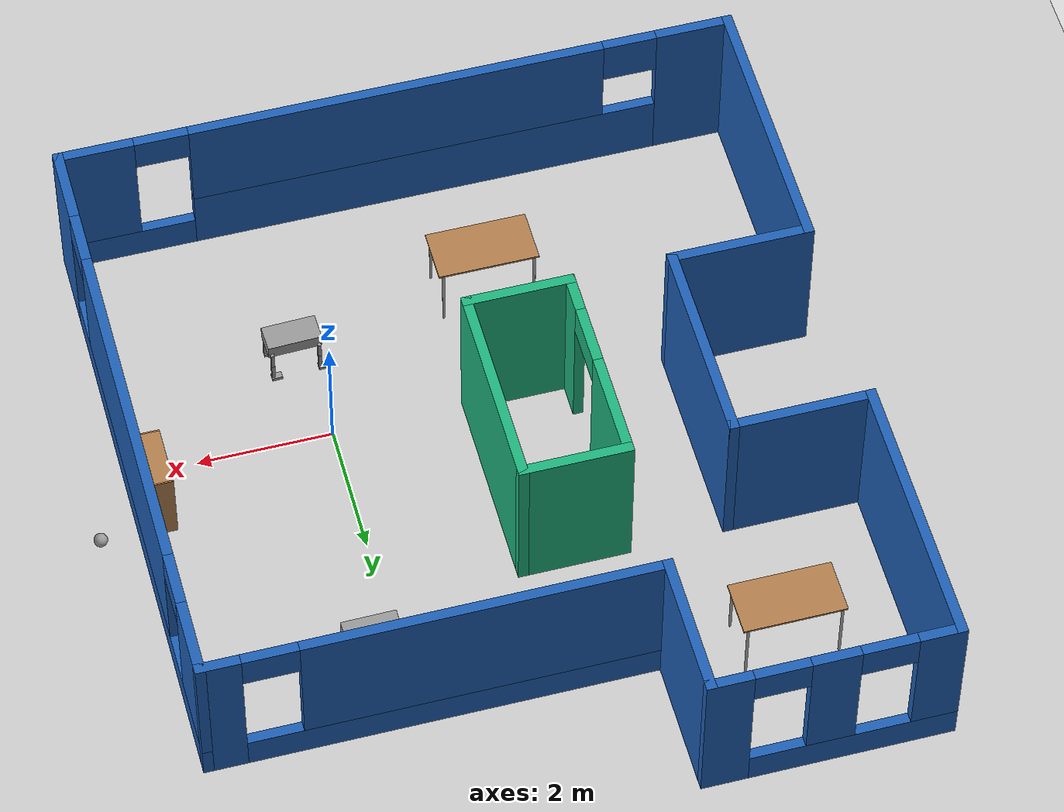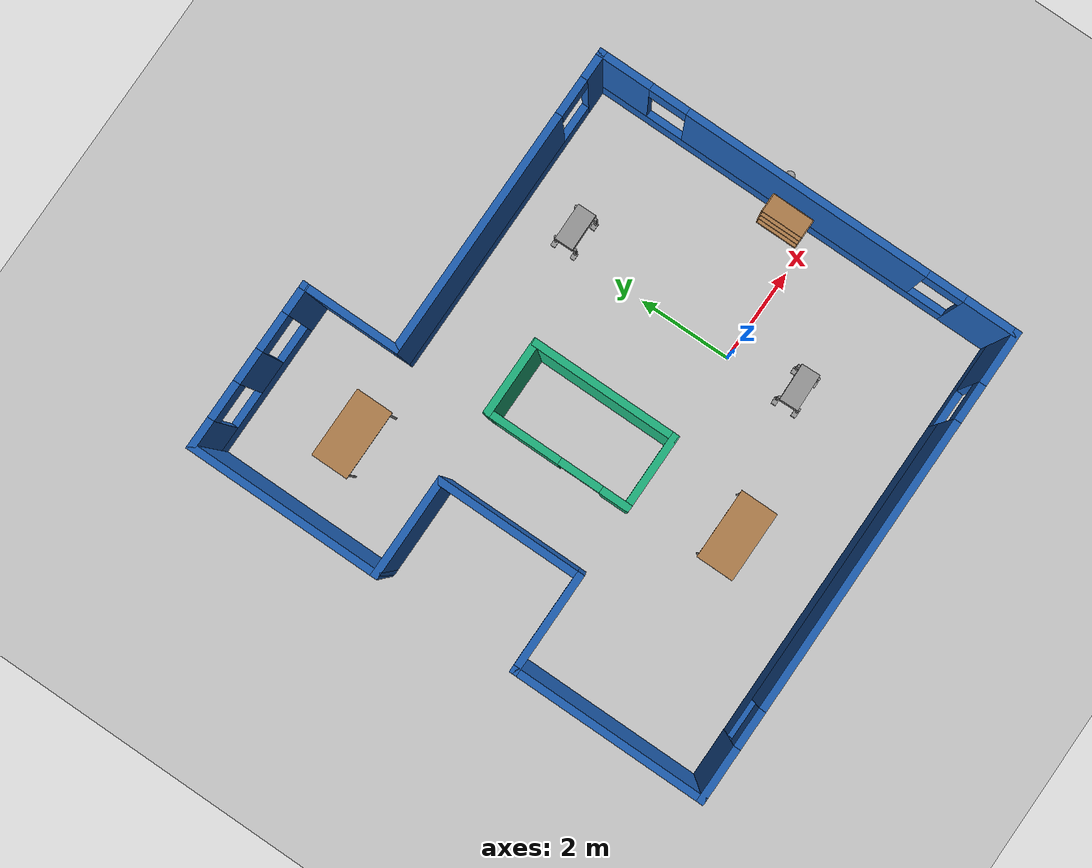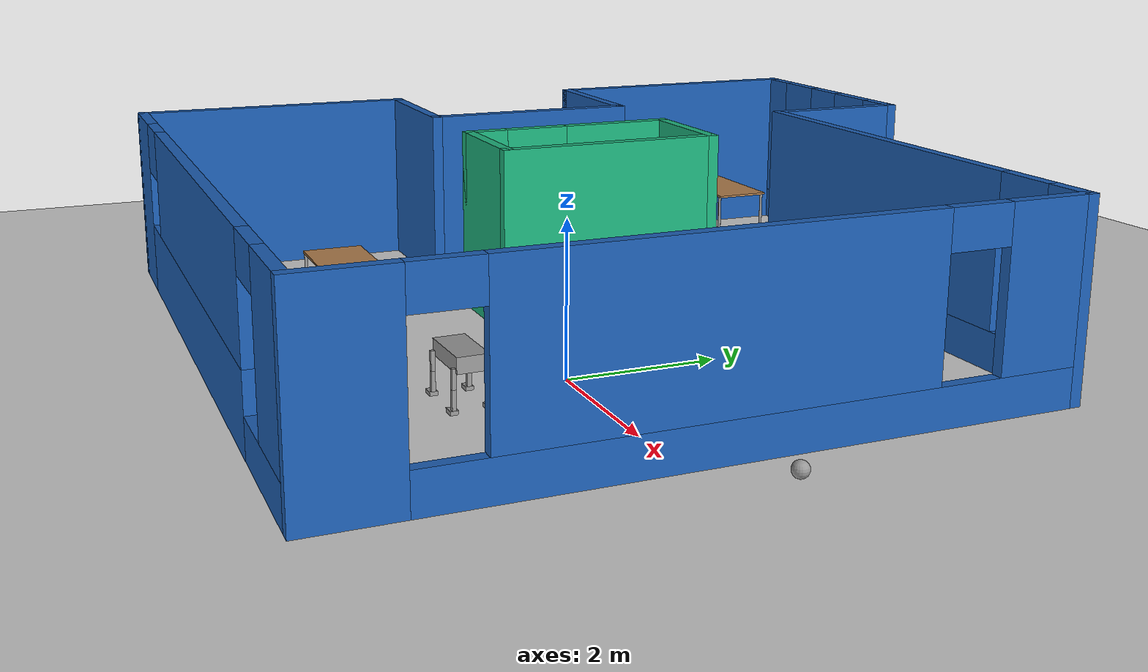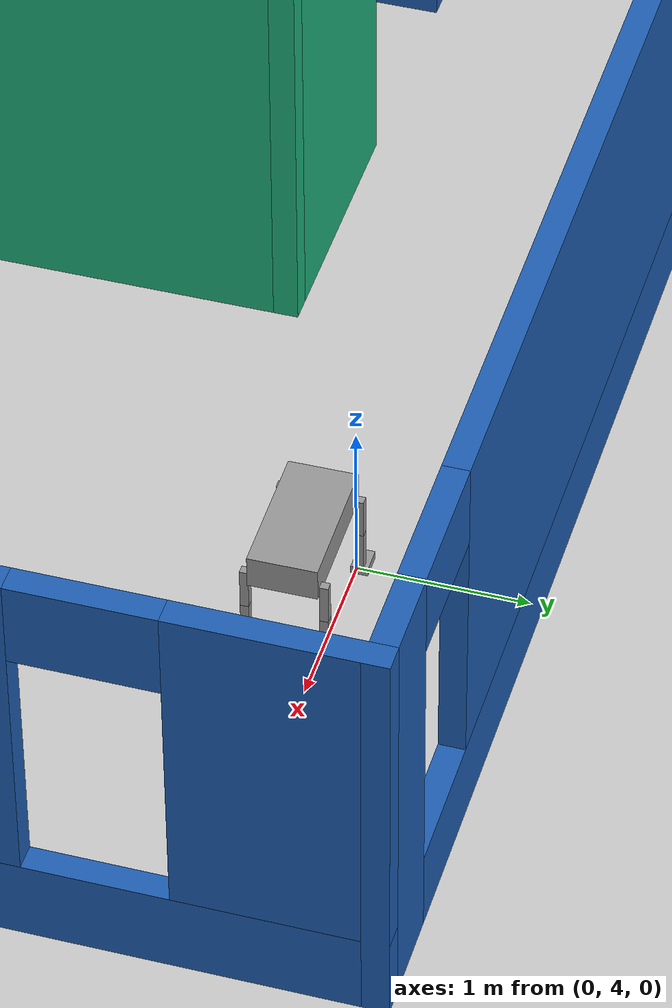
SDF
<sdf version="1.6">
 <world name="default">
  <plugin name="welcome_message" filename="libwelcome_message.so"/>
  <light name="sun" type="directional">
   <pose>0 0 10 0 -0 0</pose>
   <diffuse>0.8 0.8 0.8 1</diffuse>
   <specular>0.2 0.2 0.2 1</specular>
   <attenuation>
    <range>1000</range>
    <constant>0.9</constant>
    <linear>0.01</linear>
    <quadratic>0.001</quadratic>
   </attenuation>
   <direction>-0.5 0.1 -0.9</direction>
  </light>
  <model name="ground_plane">
   <static>1</static>
   <link name="link">
    <collision name="collision">
     <geometry><plane><normal>0 0 1</normal><size>100 100</size></plane></geometry>
     <surface><friction><ode><mu>100</mu><mu2>50</mu2></ode></friction></surface>
    </collision>
    <visual name="visual">
     <cast_shadows>0</cast_shadows>
     <geometry><plane><normal>0 0 1</normal><size>100 100</size></plane></geometry>
     <material>
      <script><uri>file://media/materials/scripts/gazebo.material</uri><name>Gazebo/Grey</name></script>
     </material>
    </visual>
   </link>
  </model>
  <gravity>0 0 -9.8</gravity>
  <magnetic_field>6e-06 2.3e-05 -4.2e-05</magnetic_field>
  <atmosphere type="adiabatic"/>
  <physics name="default_physics" default="0" type="ode">
   <max_step_size>0.001</max_step_size>
   <real_time_factor>1</real_time_factor>
   <real_time_update_rate>1000</real_time_update_rate>
  </physics>
  <scene><ambient>0.4 0.4 0.4 1</ambient><background>0.7 0.7 0.7 1</background><shadows>1</shadows></scene>
  <spherical_coordinates>
   <surface_model>EARTH_WGS84</surface_model>
   <latitude_deg>0</latitude_deg>
   <longitude_deg>0</longitude_deg>
   <elevation>0</elevation>
   <heading_deg>0</heading_deg>
  </spherical_coordinates>
  <model name="house">
   <pose>-2 1.5 0 0 -0 0</pose>
   <link name="Wall_10">
    <collision name="Wall_10_Collision">
     <geometry><box><size>2.14909 0.15 2.5</size></box></geometry>
     <pose>0 0 1.25 0 -0 0</pose>
    </collision>
    <visual name="Wall_10_Visual">
     <pose>0 0 1.25 0 -0 0</pose>
     <geometry><box><size>2.14909 0.15 2.5</size></box></geometry>
     <material>
      <script><uri>file://media/materials/scripts/gazebo.material</uri><name>Gazebo/Grey</name></script>
      <ambient>0.117647 0.376471 0.709804 1</ambient>
     </material>
     <meta><layer>0</layer></meta>
    </visual>
    <pose>-1.5 4.5 0 0 -0 1.5708</pose>
   </link>
   <link name="Wall_11">
    <pose>-3.25 5.5 0 0 -0 3.14159</pose>
    <visual name="Wall_11_Visual_0">
     <pose>-1.4875 0 1.25 0 -0 0</pose>
     <geometry><box><size>0.675 0.15 2.5</size></box></geometry>
     <material>
      <script><uri>file://media/materials/scripts/gazebo.material</uri><name>Gazebo/Grey</name></script>
      <ambient>0.117647 0.376471 0.709804 1</ambient>
     </material>
     <meta><layer>0</layer></meta>
    </visual>
    <collision name="Wall_11_Collision_0">
     <geometry><box><size>0.675 0.15 2.5</size></box></geometry>
     <pose>-1.4875 0 1.25 0 -0 0</pose>
    </collision>
    <visual name="Wall_11_Visual_1">
     <pose>0.3375 0 0.25 0 -0 0</pose>
     <geometry><box><size>2.975 0.15 0.5</size></box></geometry>
     <material>
      <script><uri>file://media/materials/scripts/gazebo.material</uri><name>Gazebo/Grey</name></script>
      <ambient>0.117647 0.376471 0.709804 1</ambient>
     </material>
     <meta><layer>0</layer></meta>
    </visual>
    <collision name="Wall_11_Collision_1">
     <geometry><box><size>2.975 0.15 0.5</size></box></geometry>
     <pose>0.3375 0 0.25 0 -0 0</pose>
    </collision>
    <visual name="Wall_11_Visual_2">
     <pose>0 0 1.5 0 -0 0</pose>
     <geometry><box><size>0.7 0.15 2</size></box></geometry>
     <material>
      <script><uri>file://media/materials/scripts/gazebo.material</uri><name>Gazebo/Grey</name></script>
      <ambient>0.117647 0.376471 0.709804 1</ambient>
     </material>
     <meta><layer>0</layer></meta>
    </visual>
    <collision name="Wall_11_Collision_2">
     <geometry><box><size>0.7 0.15 2</size></box></geometry>
     <pose>0 0 1.5 0 -0 0</pose>
    </collision>
    <visual name="Wall_11_Visual_3">
     <pose>1.4875 0 1.5 0 -0 0</pose>
     <geometry><box><size>0.675 0.15 2</size></box></geometry>
     <material>
      <script><uri>file://media/materials/scripts/gazebo.material</uri><name>Gazebo/Grey</name></script>
      <ambient>0.117647 0.376471 0.709804 1</ambient>
     </material>
     <meta><layer>0</layer></meta>
    </visual>
    <collision name="Wall_11_Collision_3">
     <geometry><box><size>0.675 0.15 2</size></box></geometry>
     <pose>1.4875 0 1.5 0 -0 0</pose>
    </collision>
    <visual name="Wall_11_Visual_4">
     <pose>-0.75 0 2.25 0 -0 0</pose>
     <geometry><box><size>0.8 0.15 0.5</size></box></geometry>
     <material>
      <script><uri>file://media/materials/scripts/gazebo.material</uri><name>Gazebo/Grey</name></script>
      <ambient>0.117647 0.376471 0.709804 1</ambient>
     </material>
     <meta><layer>0</layer></meta>
    </visual>
    <collision name="Wall_11_Collision_4">
     <geometry><box><size>0.8 0.15 0.5</size></box></geometry>
     <pose>-0.75 0 2.25 0 -0 0</pose>
    </collision>
    <visual name="Wall_11_Visual_5">
     <pose>0.75 0 2.25 0 -0 0</pose>
     <geometry><box><size>0.8 0.15 0.5</size></box></geometry>
     <material>
      <script><uri>file://media/materials/scripts/gazebo.material</uri><name>Gazebo/Grey</name></script>
      <ambient>0.117647 0.376471 0.709804 1</ambient>
     </material>
     <meta><layer>0</layer></meta>
    </visual>
    <collision name="Wall_11_Collision_5">
     <geometry><box><size>0.8 0.15 0.5</size></box></geometry>
     <pose>0.75 0 2.25 0 -0 0</pose>
    </collision>
   </link>
   <link name="Wall_13">
    <pose>-1.5 0 0 0 0 -1.5708</pose>
    <visual name="Wall_13_Visual_0">
     <pose>-0.7625 0 1.25 0 -0 0</pose>
     <geometry><box><size>1.625 0.15 2.5</size></box></geometry>
     <material>
      <script><uri>file://media/materials/scripts/gazebo.material</uri><name>Gazebo/Grey</name></script>
      <ambient>0.117647 0.709804 0.494118 1</ambient>
     </material>
     <meta><layer>0</layer></meta>
    </visual>
    <collision name="Wall_13_Collision_0">
     <geometry><box><size>1.625 0.15 2.5</size></box></geometry>
     <pose>-0.7625 0 1.25 0 -0 0</pose>
    </collision>
    <visual name="Wall_13_Visual_1">
     <pose>1.2625 0 1.25 0 -0 0</pose>
     <geometry><box><size>0.625 0.15 2.5</size></box></geometry>
     <material>
      <script><uri>file://media/materials/scripts/gazebo.material</uri><name>Gazebo/Grey</name></script>
      <ambient>0.117647 0.709804 0.494118 1</ambient>
     </material>
     <meta><layer>0</layer></meta>
    </visual>
    <collision name="Wall_13_Collision_1">
     <geometry><box><size>0.625 0.15 2.5</size></box></geometry>
     <pose>1.2625 0 1.25 0 -0 0</pose>
    </collision>
    <visual name="Wall_13_Visual_2">
     <pose>0.5 0 2.25 0 -0 0</pose>
     <geometry><box><size>0.9 0.15 0.5</size></box></geometry>
     <material>
      <script><uri>file://media/materials/scripts/gazebo.material</uri><name>Gazebo/Grey</name></script>
      <ambient>0.117647 0.709804 0.494118 1</ambient>
     </material>
     <meta><layer>0</layer></meta>
    </visual>
    <collision name="Wall_13_Collision_2">
     <geometry><box><size>0.9 0.15 0.5</size></box></geometry>
     <pose>0.5 0 2.25 0 -0 0</pose>
    </collision>
   </link>
   <link name="Wall_14">
    <collision name="Wall_14_Collision">
     <geometry><box><size>1.65 0.15 2.5</size></box></geometry>
     <pose>0 0 1.25 0 -0 0</pose>
    </collision>
    <visual name="Wall_14_Visual">
     <pose>0 0 1.25 0 -0 0</pose>
     <geometry><box><size>1.65 0.15 2.5</size></box></geometry>
     <material>
      <script><uri>file://media/materials/scripts/gazebo.material</uri><name>Gazebo/Grey</name></script>
      <ambient>0.117647 0.709804 0.494118 1</ambient>
     </material>
     <meta><layer>0</layer></meta>
    </visual>
    <pose>-0.75 -1.5 0 0 -0 0</pose>
   </link>
   <link name="Wall_15">
    <collision name="Wall_15_Collision">
     <geometry><box><size>3.15 0.15 2.5</size></box></geometry>
     <pose>0 0 1.25 0 -0 0</pose>
    </collision>
    <visual name="Wall_15_Visual">
     <pose>0 0 1.25 0 -0 0</pose>
     <geometry><box><size>3.15 0.15 2.5</size></box></geometry>
     <material>
      <script><uri>file://media/materials/scripts/gazebo.material</uri><name>Gazebo/Grey</name></script>
      <ambient>0.117647 0.709804 0.494118 1</ambient>
     </material>
     <meta><layer>0</layer></meta>
    </visual>
    <pose>0 0 0 0 -0 1.5708</pose>
   </link>
   <link name="Wall_16">
    <collision name="Wall_16_Collision">
     <geometry><box><size>1.65 0.15 2.5</size></box></geometry>
     <pose>0 0 1.25 0 -0 0</pose>
    </collision>
    <visual name="Wall_16_Visual">
     <pose>0 0 1.25 0 -0 0</pose>
     <geometry><box><size>1.65 0.15 2.5</size></box></geometry>
     <material>
      <script><uri>file://media/materials/scripts/gazebo.material</uri><name>Gazebo/Grey</name></script>
      <ambient>0.117647 0.709804 0.494118 1</ambient>
     </material>
     <meta><layer>0</layer></meta>
    </visual>
    <pose>-0.75 1.5 0 0 -0 3.14159</pose>
   </link>
   <link name="Wall_2">
    <collision name="Wall_2_Collision">
     <geometry><box><size>4.15 0.15 2.5</size></box></geometry>
     <pose>0 0 1.25 0 -0 0</pose>
    </collision>
    <visual name="Wall_2_Visual">
     <pose>0 0 1.25 0 -0 0</pose>
     <geometry><box><size>4.15 0.15 2.5</size></box></geometry>
     <material>
      <script><uri>file://media/materials/scripts/gazebo.material</uri><name>Gazebo/Grey</name></script>
      <ambient>0.117647 0.376471 0.709804 1</ambient>
     </material>
     <meta><layer>0</layer></meta>
    </visual>
    <pose>-5 3.5 0 0 0 -1.5708</pose>
   </link>
   <link name="Wall_3">
    <collision name="Wall_3_Collision">
     <geometry><box><size>2.15 0.15 2.5</size></box></geometry>
     <pose>0 0 1.25 0 -0 0</pose>
    </collision>
    <visual name="Wall_3_Visual">
     <pose>0 0 1.25 0 -0 0</pose>
     <geometry><box><size>2.15 0.15 2.5</size></box></geometry>
     <material>
      <script><uri>file://media/materials/scripts/gazebo.material</uri><name>Gazebo/Grey</name></script>
      <ambient>0.117647 0.376471 0.709804 1</ambient>
     </material>
     <meta><layer>0</layer></meta>
    </visual>
    <pose>-4 1.5 0 0 -0 0</pose>
   </link>
   <link name="Wall_4">
    <collision name="Wall_4_Collision">
     <geometry><box><size>3.15 0.15 2.5</size></box></geometry>
     <pose>0 0 1.25 0 -0 0</pose>
    </collision>
    <visual name="Wall_4_Visual">
     <pose>0 0 1.25 0 -0 0</pose>
     <geometry><box><size>3.15 0.15 2.5</size></box></geometry>
     <material>
      <script><uri>file://media/materials/scripts/gazebo.material</uri><name>Gazebo/Grey</name></script>
      <ambient>0.117647 0.376471 0.709804 1</ambient>
     </material>
     <meta><layer>0</layer></meta>
    </visual>
    <pose>-3 0 0 0 0 -1.5708</pose>
   </link>
   <link name="Wall_5">
    <collision name="Wall_5_Collision">
     <geometry><box><size>2.15 0.15 2.5</size></box></geometry>
     <pose>0 0 1.25 0 -0 0</pose>
    </collision>
    <visual name="Wall_5_Visual">
     <pose>0 0 1.25 0 -0 0</pose>
     <geometry><box><size>2.15 0.15 2.5</size></box></geometry>
     <material>
      <script><uri>file://media/materials/scripts/gazebo.material</uri><name>Gazebo/Grey</name></script>
      <ambient>0.117647 0.376471 0.709804 1</ambient>
     </material>
     <meta><layer>0</layer></meta>
    </visual>
    <pose>-4 -1.5 0 0 -0 3.14159</pose>
   </link>
   <link name="Wall_6">
    <collision name="Wall_6_Collision">
     <geometry><box><size>4.15 0.15 2.5</size></box></geometry>
     <pose>0 0 1.25 0 -0 0</pose>
    </collision>
    <visual name="Wall_6_Visual">
     <pose>0 0 1.25 0 -0 0</pose>
     <geometry><box><size>4.15 0.15 2.5</size></box></geometry>
     <material>
      <script><uri>file://media/materials/scripts/gazebo.material</uri><name>Gazebo/Grey</name></script>
      <ambient>0.117647 0.376471 0.709804 1</ambient>
     </material>
     <meta><layer>0</layer></meta>
    </visual>
    <pose>-5 -3.5 0 0 0 -1.5708</pose>
   </link>
   <link name="Wall_7">
    <pose>0 -5.5 0 0 -0 0</pose>
    <visual name="Wall_7_Visual_0">
     <pose>-4.4875 0 1.25 0 -0 0</pose>
     <geometry><box><size>1.175 0.15 2.5</size></box></geometry>
     <material>
      <script><uri>file://media/materials/scripts/gazebo.material</uri><name>Gazebo/Grey</name></script>
      <ambient>0.117647 0.376471 0.709804 1</ambient>
     </material>
     <meta><layer>0</layer></meta>
    </visual>
    <collision name="Wall_7_Collision_0">
     <geometry><box><size>1.175 0.15 2.5</size></box></geometry>
     <pose>-4.4875 0 1.25 0 -0 0</pose>
    </collision>
    <visual name="Wall_7_Visual_1">
     <pose>-0.4 0 0.5 0 -0 0</pose>
     <geometry><box><size>7 0.15 1</size></box></geometry>
     <material>
      <script><uri>file://media/materials/scripts/gazebo.material</uri><name>Gazebo/Grey</name></script>
      <ambient>0.117647 0.376471 0.709804 1</ambient>
     </material>
     <meta><layer>0</layer></meta>
    </visual>
    <collision name="Wall_7_Collision_1">
     <geometry><box><size>7 0.15 1</size></box></geometry>
     <pose>-0.4 0 0.5 0 -0 0</pose>
    </collision>
    <visual name="Wall_7_Visual_2">
     <pose>4.0875 0 0.25 0 -0 0</pose>
     <geometry><box><size>1.975 0.15 0.5</size></box></geometry>
     <material>
      <script><uri>file://media/materials/scripts/gazebo.material</uri><name>Gazebo/Grey</name></script>
      <ambient>0.117647 0.376471 0.709804 1</ambient>
     </material>
     <meta><layer>0</layer></meta>
    </visual>
    <collision name="Wall_7_Collision_2">
     <geometry><box><size>1.975 0.15 0.5</size></box></geometry>
     <pose>4.0875 0 0.25 0 -0 0</pose>
    </collision>
    <visual name="Wall_7_Visual_3">
     <pose>4.4875 0 1.5 0 -0 0</pose>
     <geometry><box><size>1.175 0.15 2</size></box></geometry>
     <material>
      <script><uri>file://media/materials/scripts/gazebo.material</uri><name>Gazebo/Grey</name></script>
      <ambient>0.117647 0.376471 0.709804 1</ambient>
     </material>
     <meta><layer>0</layer></meta>
    </visual>
    <collision name="Wall_7_Collision_3">
     <geometry><box><size>1.175 0.15 2</size></box></geometry>
     <pose>4.4875 0 1.5 0 -0 0</pose>
    </collision>
    <visual name="Wall_7_Visual_4">
     <pose>-0 0 1.75 0 -0 0</pose>
     <geometry><box><size>6.2 0.15 1.5</size></box></geometry>
     <material>
      <script><uri>file://media/materials/scripts/gazebo.material</uri><name>Gazebo/Grey</name></script>
      <ambient>0.117647 0.376471 0.709804 1</ambient>
     </material>
     <meta><layer>0</layer></meta>
    </visual>
    <collision name="Wall_7_Collision_4">
     <geometry><box><size>6.2 0.15 1.5</size></box></geometry>
     <pose>-0 0 1.75 0 -0 0</pose>
    </collision>
    <visual name="Wall_7_Visual_5">
     <pose>-3.5 0 2.15 0 -0 0</pose>
     <geometry><box><size>0.8 0.15 0.7</size></box></geometry>
     <material>
      <script><uri>file://media/materials/scripts/gazebo.material</uri><name>Gazebo/Grey</name></script>
      <ambient>0.117647 0.376471 0.709804 1</ambient>
     </material>
     <meta><layer>0</layer></meta>
    </visual>
    <collision name="Wall_7_Collision_5">
     <geometry><box><size>0.8 0.15 0.7</size></box></geometry>
     <pose>-3.5 0 2.15 0 -0 0</pose>
    </collision>
    <visual name="Wall_7_Visual_6">
     <pose>3.5 0 2.25 0 -0 0</pose>
     <geometry><box><size>0.8 0.15 0.5</size></box></geometry>
     <material>
      <script><uri>file://media/materials/scripts/gazebo.material</uri><name>Gazebo/Grey</name></script>
      <ambient>0.117647 0.376471 0.709804 1</ambient>
     </material>
     <meta><layer>0</layer></meta>
    </visual>
    <collision name="Wall_7_Collision_6">
     <geometry><box><size>0.8 0.15 0.5</size></box></geometry>
     <pose>3.5 0 2.25 0 -0 0</pose>
    </collision>
   </link>
   <link name="Wall_8">
    <pose>5 -1 0 0 -0 1.5708</pose>
    <visual name="Wall_8_Visual_0">
     <pose>-3.9875 0 1.25 0 -0 0</pose>
     <geometry><box><size>1.175 0.15 2.5</size></box></geometry>
     <material>
      <script><uri>file://media/materials/scripts/gazebo.material</uri><name>Gazebo/Grey</name></script>
      <ambient>0.117647 0.376471 0.709804 1</ambient>
     </material>
     <meta><layer>0</layer></meta>
    </visual>
    <collision name="Wall_8_Collision_0">
     <geometry><box><size>1.175 0.15 2.5</size></box></geometry>
     <pose>-3.9875 0 1.25 0 -0 0</pose>
    </collision>
    <visual name="Wall_8_Visual_1">
     <pose>0.5875 0 0.25 0 -0 0</pose>
     <geometry><box><size>7.975 0.15 0.5</size></box></geometry>
     <material>
      <script><uri>file://media/materials/scripts/gazebo.material</uri><name>Gazebo/Grey</name></script>
      <ambient>0.117647 0.376471 0.709804 1</ambient>
     </material>
     <meta><layer>0</layer></meta>
    </visual>
    <collision name="Wall_8_Collision_1">
     <geometry><box><size>7.975 0.15 0.5</size></box></geometry>
     <pose>0.5875 0 0.25 0 -0 0</pose>
    </collision>
    <visual name="Wall_8_Visual_2">
     <pose>0.004987 0 1.5 0 -0 0</pose>
     <geometry><box><size>5.20997 0.15 2</size></box></geometry>
     <material>
      <script><uri>file://media/materials/scripts/gazebo.material</uri><name>Gazebo/Grey</name></script>
      <ambient>0.117647 0.376471 0.709804 1</ambient>
     </material>
     <meta><layer>0</layer></meta>
    </visual>
    <collision name="Wall_8_Collision_2">
     <geometry><box><size>5.20997 0.15 2</size></box></geometry>
     <pose>0.004987 0 1.5 0 -0 0</pose>
    </collision>
    <visual name="Wall_8_Visual_3">
     <pose>3.99249 0 1.5 0 -0 0</pose>
     <geometry><box><size>1.16503 0.15 2</size></box></geometry>
     <material>
      <script><uri>file://media/materials/scripts/gazebo.material</uri><name>Gazebo/Grey</name></script>
      <ambient>0.117647 0.376471 0.709804 1</ambient>
     </material>
     <meta><layer>0</layer></meta>
    </visual>
    <collision name="Wall_8_Collision_3">
     <geometry><box><size>1.16503 0.15 2</size></box></geometry>
     <pose>3.99249 0 1.5 0 -0 0</pose>
    </collision>
    <visual name="Wall_8_Visual_4">
     <pose>-3 0 2.25 0 -0 0</pose>
     <geometry><box><size>0.8 0.15 0.5</size></box></geometry>
     <material>
      <script><uri>file://media/materials/scripts/gazebo.material</uri><name>Gazebo/Grey</name></script>
      <ambient>0.117647 0.376471 0.709804 1</ambient>
     </material>
     <meta><layer>0</layer></meta>
    </visual>
    <collision name="Wall_8_Collision_4">
     <geometry><box><size>0.8 0.15 0.5</size></box></geometry>
     <pose>-3 0 2.25 0 -0 0</pose>
    </collision>
    <visual name="Wall_8_Visual_5">
     <pose>3.00997 0 2.25 0 -0 0</pose>
     <geometry><box><size>0.8 0.15 0.5</size></box></geometry>
     <material>
      <script><uri>file://media/materials/scripts/gazebo.material</uri><name>Gazebo/Grey</name></script>
      <ambient>0.117647 0.376471 0.709804 1</ambient>
     </material>
     <meta><layer>0</layer></meta>
    </visual>
    <collision name="Wall_8_Collision_5">
     <geometry><box><size>0.8 0.15 0.5</size></box></geometry>
     <pose>3.00997 0 2.25 0 -0 0</pose>
    </collision>
   </link>
   <link name="Wall_9">
    <pose>1.75 3.5 0 0 -0 3.14159</pose>
    <visual name="Wall_9_Visual_0">
     <pose>-3.00663 0 1.25 0 -0 0</pose>
     <geometry><box><size>0.636747 0.15 2.5</size></box></geometry>
     <material>
      <script><uri>file://media/materials/scripts/gazebo.material</uri><name>Gazebo/Grey</name></script>
      <ambient>0.117647 0.376471 0.709804 1</ambient>
     </material>
     <meta><layer>0</layer></meta>
    </visual>
    <collision name="Wall_9_Collision_0">
     <geometry><box><size>0.636747 0.15 2.5</size></box></geometry>
     <pose>-3.00663 0 1.25 0 -0 0</pose>
    </collision>
    <visual name="Wall_9_Visual_1">
     <pose>0.318374 0 0.25 0 -0 0</pose>
     <geometry><box><size>6.01325 0.15 0.5</size></box></geometry>
     <material>
      <script><uri>file://media/materials/scripts/gazebo.material</uri><name>Gazebo/Grey</name></script>
      <ambient>0.117647 0.376471 0.709804 1</ambient>
     </material>
     <meta><layer>0</layer></meta>
    </visual>
    <collision name="Wall_9_Collision_1">
     <geometry><box><size>6.01325 0.15 0.5</size></box></geometry>
     <pose>0.318374 0 0.25 0 -0 0</pose>
    </collision>
    <visual name="Wall_9_Visual_2">
     <pose>0.718374 0 1.5 0 -0 0</pose>
     <geometry><box><size>5.21325 0.15 2</size></box></geometry>
     <material>
      <script><uri>file://media/materials/scripts/gazebo.material</uri><name>Gazebo/Grey</name></script>
      <ambient>0.117647 0.376471 0.709804 1</ambient>
     </material>
     <meta><layer>0</layer></meta>
    </visual>
    <collision name="Wall_9_Collision_2">
     <geometry><box><size>5.21325 0.15 2</size></box></geometry>
     <pose>0.718374 0 1.5 0 -0 0</pose>
    </collision>
    <visual name="Wall_9_Visual_3">
     <pose>-2.28825 0 2.25 0 -0 0</pose>
     <geometry><box><size>0.8 0.15 0.5</size></box></geometry>
     <material>
      <script><uri>file://media/materials/scripts/gazebo.material</uri><name>Gazebo/Grey</name></script>
      <ambient>0.117647 0.376471 0.709804 1</ambient>
     </material>
     <meta><layer>0</layer></meta>
    </visual>
    <collision name="Wall_9_Collision_3">
     <geometry><box><size>0.8 0.15 0.5</size></box></geometry>
     <pose>-2.28825 0 2.25 0 -0 0</pose>
    </collision>
   </link>
   <static>1</static>
  </model>
  <model name="table">
   <static>1</static>
   <link name="link">
    <collision name="surface">
     <pose>0 0 1 0 -0 0</pose>
     <geometry><box><size>1.5 0.8 0.03</size></box></geometry>
     <surface><friction><ode><mu>0.6</mu><mu2>0.6</mu2></ode></friction></surface>
    </collision>
    <visual name="visual1">
     <pose>0 0 1 0 -0 0</pose>
     <geometry><box><size>1.5 0.8 0.03</size></box></geometry>
     <material>
      <script><uri>file://media/materials/scripts/gazebo.material</uri><name>Gazebo/Wood</name></script>
     </material>
    </visual>
    <collision name="front_left_leg">
     <pose>0.68 0.38 0.5 0 -0 0</pose>
     <geometry><cylinder><radius>0.02</radius><length>1</length></cylinder></geometry>
    </collision>
    <visual name="front_left_leg">
     <pose>0.68 0.38 0.5 0 -0 0</pose>
     <geometry><cylinder><radius>0.02</radius><length>1</length></cylinder></geometry>
     <material>
      <script><uri>file://media/materials/scripts/gazebo.material</uri><name>Gazebo/Grey</name></script>
     </material>
    </visual>
    <collision name="front_right_leg">
     <pose>0.68 -0.38 0.5 0 -0 0</pose>
     <geometry><cylinder><radius>0.02</radius><length>1</length></cylinder></geometry>
    </collision>
    <visual name="front_right_leg">
     <pose>0.68 -0.38 0.5 0 -0 0</pose>
     <geometry><cylinder><radius>0.02</radius><length>1</length></cylinder></geometry>
     <material>
      <script><uri>file://media/materials/scripts/gazebo.material</uri><name>Gazebo/Grey</name></script>
     </material>
    </visual>
    <collision name="back_right_leg">
     <pose>-0.68 -0.38 0.5 0 -0 0</pose>
     <geometry><cylinder><radius>0.02</radius><length>1</length></cylinder></geometry>
    </collision>
    <visual name="back_right_leg">
     <pose>-0.68 -0.38 0.5 0 -0 0</pose>
     <geometry><cylinder><radius>0.02</radius><length>1</length></cylinder></geometry>
     <material>
      <script><uri>file://media/materials/scripts/gazebo.material</uri><name>Gazebo/Grey</name></script>
     </material>
    </visual>
    <collision name="back_left_leg">
     <pose>-0.68 0.38 0.5 0 -0 0</pose>
     <geometry><cylinder><radius>0.02</radius><length>1</length></cylinder></geometry>
    </collision>
    <visual name="back_left_leg">
     <pose>-0.68 0.38 0.5 0 -0 0</pose>
     <geometry><cylinder><radius>0.02</radius><length>1</length></cylinder></geometry>
     <material>
      <script><uri>file://media/materials/scripts/gazebo.material</uri><name>Gazebo/Grey</name></script>
     </material>
    </visual>
   </link>
   <pose>-2.75 -2 0 0 -0 0</pose>
  </model>
  <model name="bookshelf">
   <static>1</static>
   <link name="link">
    <inertial><mass>1</mass></inertial>
    <collision name="back">
     <pose>0 0.005 0.6 0 -0 0</pose>
     <geometry><box><size>0.9 0.01 1.2</size></box></geometry>
    </collision>
    <visual name="visual1">
     <pose>0 0.005 0.6 0 -0 0</pose>
     <geometry><box><size>0.9 0.01 1.2</size></box></geometry>
     <material>
      <script><uri>file://media/materials/scripts/gazebo.material</uri><name>Gazebo/Wood</name></script>
     </material>
    </visual>
    <collision name="left_side">
     <pose>0.45 -0.195 0.6 0 -0 0</pose>
     <geometry><box><size>0.02 0.4 1.2</size></box></geometry>
    </collision>
    <visual name="visual2">
     <pose>0.45 -0.195 0.6 0 -0 0</pose>
     <geometry><box><size>0.02 0.4 1.2</size></box></geometry>
     <material>
      <script><uri>file://media/materials/scripts/gazebo.material</uri><name>Gazebo/Wood</name></script>
     </material>
    </visual>
    <collision name="right_side">
     <pose>-0.45 -0.195 0.6 0 -0 0</pose>
     <geometry><box><size>0.02 0.4 1.2</size></box></geometry>
    </collision>
    <visual name="visual3">
     <pose>-0.45 -0.195 0.6 0 -0 0</pose>
     <geometry><box><size>0.02 0.4 1.2</size></box></geometry>
     <material>
      <script><uri>file://media/materials/scripts/gazebo.material</uri><name>Gazebo/Wood</name></script>
     </material>
    </visual>
    <collision name="bottom">
     <pose>0 -0.195 0.03 0 -0 0</pose>
     <geometry><box><size>0.88 0.4 0.06</size></box></geometry>
    </collision>
    <visual name="visual4">
     <pose>0 -0.195 0.03 0 -0 0</pose>
     <geometry><box><size>0.88 0.4 0.06</size></box></geometry>
     <material>
      <script><uri>file://media/materials/scripts/gazebo.material</uri><name>Gazebo/Wood</name></script>
     </material>
    </visual>
    <collision name="top">
     <pose>0 -0.195 1.19 0 -0 0</pose>
     <geometry><box><size>0.88 0.4 0.02</size></box></geometry>
    </collision>
    <visual name="visual5">
     <pose>0 -0.195 1.19 0 -0 0</pose>
     <geometry><box><size>0.88 0.4 0.02</size></box></geometry>
     <material>
      <script><uri>file://media/materials/scripts/gazebo.material</uri><name>Gazebo/Wood</name></script>
     </material>
    </visual>
    <collision name="low_shelf">
     <pose>0 -0.195 0.43 0 -0 0</pose>
     <geometry><box><size>0.88 0.4 0.02</size></box></geometry>
    </collision>
    <visual name="visual6">
     <pose>0 -0.195 0.43 0 -0 0</pose>
     <geometry><box><size>0.88 0.4 0.02</size></box></geometry>
     <material>
      <script><uri>file://media/materials/scripts/gazebo.material</uri><name>Gazebo/Wood</name></script>
     </material>
    </visual>
    <collision name="high_shelf">
     <pose>0 -0.195 0.8 0 -0 0</pose>
     <geometry><box><size>0.88 0.4 0.02</size></box></geometry>
    </collision>
    <visual name="visual7">
     <pose>0 -0.195 0.8 0 -0 0</pose>
     <geometry><box><size>0.88 0.4 0.02</size></box></geometry>
     <material>
      <script><uri>file://media/materials/scripts/gazebo.material</uri><name>Gazebo/Wood</name></script>
     </material>
    </visual>
   </link>
   <pose>2.91289 0.586626 0 0 0 -1.5708</pose>
  </model>
  <model name="table_0">
   <static>1</static>
   <link name="link">
    <collision name="surface">
     <pose>0 0 1 0 -0 0</pose>
     <geometry><box><size>1.5 0.8 0.03</size></box></geometry>
     <surface><friction><ode><mu>0.6</mu><mu2>0.6</mu2></ode></friction></surface>
    </collision>
    <visual name="visual1">
     <pose>0 0 1 0 -0 0</pose>
     <geometry><box><size>1.5 0.8 0.03</size></box></geometry>
     <material>
      <script><uri>file://media/materials/scripts/gazebo.material</uri><name>Gazebo/Wood</name></script>
     </material>
    </visual>
    <collision name="front_left_leg">
     <pose>0.68 0.38 0.5 0 -0 0</pose>
     <geometry><cylinder><radius>0.02</radius><length>1</length></cylinder></geometry>
    </collision>
    <visual name="front_left_leg">
     <pose>0.68 0.38 0.5 0 -0 0</pose>
     <geometry><cylinder><radius>0.02</radius><length>1</length></cylinder></geometry>
     <material>
      <script><uri>file://media/materials/scripts/gazebo.material</uri><name>Gazebo/Grey</name></script>
     </material>
    </visual>
    <collision name="front_right_leg">
     <pose>0.68 -0.38 0.5 0 -0 0</pose>
     <geometry><cylinder><radius>0.02</radius><length>1</length></cylinder></geometry>
    </collision>
    <visual name="front_right_leg">
     <pose>0.68 -0.38 0.5 0 -0 0</pose>
     <geometry><cylinder><radius>0.02</radius><length>1</length></cylinder></geometry>
     <material>
      <script><uri>file://media/materials/scripts/gazebo.material</uri><name>Gazebo/Grey</name></script>
     </material>
    </visual>
    <collision name="back_right_leg">
     <pose>-0.68 -0.38 0.5 0 -0 0</pose>
     <geometry><cylinder><radius>0.02</radius><length>1</length></cylinder></geometry>
    </collision>
    <visual name="back_right_leg">
     <pose>-0.68 -0.38 0.5 0 -0 0</pose>
     <geometry><cylinder><radius>0.02</radius><length>1</length></cylinder></geometry>
     <material>
      <script><uri>file://media/materials/scripts/gazebo.material</uri><name>Gazebo/Grey</name></script>
     </material>
    </visual>
    <collision name="back_left_leg">
     <pose>-0.68 0.38 0.5 0 -0 0</pose>
     <geometry><cylinder><radius>0.02</radius><length>1</length></cylinder></geometry>
    </collision>
    <visual name="back_left_leg">
     <pose>-0.68 0.38 0.5 0 -0 0</pose>
     <geometry><cylinder><radius>0.02</radius><length>1</length></cylinder></geometry>
     <material>
      <script><uri>file://media/materials/scripts/gazebo.material</uri><name>Gazebo/Grey</name></script>
     </material>
    </visual>
   </link>
   <pose>-5.25 5 0 0 -0 0</pose>
  </model>
  <model name="robot">
   <link name="link_0">
    <pose>-0 -5 1 0 -0 0</pose>
    <inertial>
     <mass>1</mass>
     <inertia>
      <ixx>0.166667</ixx>
      <ixy>0</ixy>
      <ixz>0</ixz>
      <iyy>0.166667</iyy>
      <iyz>0</iyz>
      <izz>0.166667</izz>
     </inertia>
    </inertial>
    <visual name="visual">
     <geometry><box><size>0.8 0.4 0.2</size></box></geometry>
     <material>
      <lighting>1</lighting>
      <script><uri>file://media/materials/scripts/gazebo.material</uri><name>Gazebo/Grey</name></script>
      <shader type="pixel"><normal_map>__default__</normal_map></shader>
      <ambient>0.3 0.3 0.3 1</ambient>
      <diffuse>0.7 0.7 0.7 1</diffuse>
      <specular>0.01 0.01 0.01 1</specular>
      <emissive>0 0 0 1</emissive>
     </material>
    </visual>
    <collision name="collision">
     <geometry><box><size>0.8 0.4 0.2</size></box></geometry>
     <surface>
      <friction>
       <ode><mu>1</mu><mu2>1</mu2><fdir1>0 0 0</fdir1><slip1>0</slip1><slip2>0</slip2></ode>
       <torsional>
        <coefficient>1</coefficient>
        <patch_radius>0</patch_radius>
        <surface_radius>0</surface_radius>
        <use_patch_radius>1</use_patch_radius>
        <ode><slip>0</slip></ode>
       </torsional>
      </friction>
      <bounce><restitution_coefficient>0</restitution_coefficient><threshold>1e+06</threshold></bounce>
      <contact>
       <collide_without_contact>0</collide_without_contact>
       <collide_without_contact_bitmask>1</collide_without_contact_bitmask>
       <collide_bitmask>1</collide_bitmask>
       <ode>
        <soft_cfm>0</soft_cfm>
        <soft_erp>0.2</soft_erp>
        <kp>1e+13</kp>
        <kd>1</kd>
        <max_vel>0.01</max_vel>
        <min_depth>0</min_depth>
       </ode>
       <bullet>
        <split_impulse>1</split_impulse>
        <split_impulse_penetration_threshold>-0.01</split_impulse_penetration_threshold>
        <soft_cfm>0</soft_cfm>
        <soft_erp>0.2</soft_erp>
        <kp>1e+13</kp>
        <kd>1</kd>
       </bullet>
      </contact>
     </surface>
    </collision>
   </link>
   <link name="link_0_0">
    <pose>-0.4 -5.225 0.4375 0 -0 0</pose>
    <inertial>
     <mass>1</mass>
     <inertia>
      <ixx>0.166667</ixx>
      <ixy>0</ixy>
      <ixz>0</ixz>
      <iyy>0.166667</iyy>
      <iyz>0</iyz>
      <izz>0.166667</izz>
     </inertia>
    </inertial>
    <visual name="visual">
     <geometry><box><size>0.15 0.1 0.05</size></box></geometry>
     <material>
      <lighting>1</lighting>
      <script><uri>file://media/materials/scripts/gazebo.material</uri><name>Gazebo/Grey</name></script>
      <shader type="pixel"><normal_map>__default__</normal_map></shader>
      <ambient>0.3 0.3 0.3 1</ambient>
      <diffuse>0.7 0.7 0.7 1</diffuse>
      <specular>0.01 0.01 0.01 1</specular>
      <emissive>0 0 0 1</emissive>
     </material>
    </visual>
    <collision name="collision">
     <geometry><box><size>0.15 0.1 0.05</size></box></geometry>
     <surface>
      <friction>
       <ode><mu>1</mu><mu2>1</mu2><fdir1>0 0 0</fdir1><slip1>0</slip1><slip2>0</slip2></ode>
       <torsional>
        <coefficient>1</coefficient>
        <patch_radius>0</patch_radius>
        <surface_radius>0</surface_radius>
        <use_patch_radius>1</use_patch_radius>
        <ode><slip>0</slip></ode>
       </torsional>
      </friction>
      <bounce><restitution_coefficient>0</restitution_coefficient><threshold>1e+06</threshold></bounce>
      <contact>
       <collide_without_contact>0</collide_without_contact>
       <collide_without_contact_bitmask>1</collide_without_contact_bitmask>
       <collide_bitmask>1</collide_bitmask>
       <ode>
        <soft_cfm>0</soft_cfm>
        <soft_erp>0.2</soft_erp>
        <kp>1e+13</kp>
        <kd>1</kd>
        <max_vel>0.01</max_vel>
        <min_depth>0</min_depth>
       </ode>
       <bullet>
        <split_impulse>1</split_impulse>
        <split_impulse_penetration_threshold>-0.01</split_impulse_penetration_threshold>
        <soft_cfm>0</soft_cfm>
        <soft_erp>0.2</soft_erp>
        <kp>1e+13</kp>
        <kd>1</kd>
       </bullet>
      </contact>
     </surface>
    </collision>
   </link>
   <link name="link_0_0_clone">
    <pose>-0.4 -4.775 0.4375 0 -0 0</pose>
    <inertial>
     <mass>1</mass>
     <inertia>
      <ixx>0.166667</ixx>
      <ixy>0</ixy>
      <ixz>0</ixz>
      <iyy>0.166667</iyy>
      <iyz>0</iyz>
      <izz>0.166667</izz>
     </inertia>
    </inertial>
    <visual name="visual_0">
     <geometry><box><size>0.15 0.1 0.05</size></box></geometry>
     <material>
      <lighting>1</lighting>
      <script><uri>file://media/materials/scripts/gazebo.material</uri><name>Gazebo/Grey</name></script>
      <shader type="pixel"><normal_map>__default__</normal_map></shader>
      <ambient>0.3 0.3 0.3 1</ambient>
      <diffuse>0.7 0.7 0.7 1</diffuse>
      <specular>0.01 0.01 0.01 1</specular>
      <emissive>0 0 0 1</emissive>
     </material>
    </visual>
    <collision name="collision">
     <geometry><box><size>0.15 0.1 0.05</size></box></geometry>
     <surface>
      <friction>
       <ode><mu>1</mu><mu2>1</mu2><fdir1>0 0 0</fdir1><slip1>0</slip1><slip2>0</slip2></ode>
       <torsional>
        <coefficient>1</coefficient>
        <patch_radius>0</patch_radius>
        <surface_radius>0</surface_radius>
        <use_patch_radius>1</use_patch_radius>
        <ode><slip>0</slip></ode>
       </torsional>
      </friction>
      <bounce><restitution_coefficient>0</restitution_coefficient><threshold>1e+06</threshold></bounce>
      <contact>
       <collide_without_contact>0</collide_without_contact>
       <collide_without_contact_bitmask>1</collide_without_contact_bitmask>
       <collide_bitmask>1</collide_bitmask>
       <ode>
        <soft_cfm>0</soft_cfm>
        <soft_erp>0.2</soft_erp>
        <kp>1e+13</kp>
        <kd>1</kd>
        <max_vel>0.01</max_vel>
        <min_depth>0</min_depth>
       </ode>
       <bullet>
        <split_impulse>1</split_impulse>
        <split_impulse_penetration_threshold>-0.01</split_impulse_penetration_threshold>
        <soft_cfm>0</soft_cfm>
        <soft_erp>0.2</soft_erp>
        <kp>1e+13</kp>
        <kd>1</kd>
       </bullet>
      </contact>
     </surface>
    </collision>
   </link>
   <link name="link_0_0_clone_0">
    <pose>0.3 -5.225 0.4375 0 -0 0</pose>
    <inertial>
     <mass>1</mass>
     <inertia>
      <ixx>0.166667</ixx>
      <ixy>0</ixy>
      <ixz>0</ixz>
      <iyy>0.166667</iyy>
      <iyz>0</iyz>
      <izz>0.166667</izz>
     </inertia>
    </inertial>
    <visual name="visual_0">
     <geometry><box><size>0.15 0.1 0.05</size></box></geometry>
     <material>
      <lighting>1</lighting>
      <script><uri>file://media/materials/scripts/gazebo.material</uri><name>Gazebo/Grey</name></script>
      <shader type="pixel"><normal_map>__default__</normal_map></shader>
      <ambient>0.3 0.3 0.3 1</ambient>
      <diffuse>0.7 0.7 0.7 1</diffuse>
      <specular>0.01 0.01 0.01 1</specular>
      <emissive>0 0 0 1</emissive>
     </material>
    </visual>
    <collision name="collision">
     <geometry><box><size>0.15 0.1 0.05</size></box></geometry>
     <surface>
      <friction>
       <ode><mu>1</mu><mu2>1</mu2><fdir1>0 0 0</fdir1><slip1>0</slip1><slip2>0</slip2></ode>
       <torsional>
        <coefficient>1</coefficient>
        <patch_radius>0</patch_radius>
        <surface_radius>0</surface_radius>
        <use_patch_radius>1</use_patch_radius>
        <ode><slip>0</slip></ode>
       </torsional>
      </friction>
      <bounce><restitution_coefficient>0</restitution_coefficient><threshold>1e+06</threshold></bounce>
      <contact>
       <collide_without_contact>0</collide_without_contact>
       <collide_without_contact_bitmask>1</collide_without_contact_bitmask>
       <collide_bitmask>1</collide_bitmask>
       <ode>
        <soft_cfm>0</soft_cfm>
        <soft_erp>0.2</soft_erp>
        <kp>1e+13</kp>
        <kd>1</kd>
        <max_vel>0.01</max_vel>
        <min_depth>0</min_depth>
       </ode>
       <bullet>
        <split_impulse>1</split_impulse>
        <split_impulse_penetration_threshold>-0.01</split_impulse_penetration_threshold>
        <soft_cfm>0</soft_cfm>
        <soft_erp>0.2</soft_erp>
        <kp>1e+13</kp>
        <kd>1</kd>
       </bullet>
      </contact>
     </surface>
    </collision>
   </link>
   <link name="link_0_0_clone_0_clone">
    <pose>0.3 -4.775 0.4375 0 -0 0</pose>
    <inertial>
     <mass>1</mass>
     <inertia>
      <ixx>0.166667</ixx>
      <ixy>0</ixy>
      <ixz>0</ixz>
      <iyy>0.166667</iyy>
      <iyz>0</iyz>
      <izz>0.166667</izz>
     </inertia>
    </inertial>
    <visual name="visual_0">
     <geometry><box><size>0.15 0.1 0.05</size></box></geometry>
     <material>
      <lighting>1</lighting>
      <script><uri>file://media/materials/scripts/gazebo.material</uri><name>Gazebo/Grey</name></script>
      <shader type="pixel"><normal_map>__default__</normal_map></shader>
      <ambient>0.3 0.3 0.3 1</ambient>
      <diffuse>0.7 0.7 0.7 1</diffuse>
      <specular>0.01 0.01 0.01 1</specular>
      <emissive>0 0 0 1</emissive>
     </material>
    </visual>
    <collision name="collision">
     <geometry><box><size>0.15 0.1 0.05</size></box></geometry>
     <surface>
      <friction>
       <ode><mu>1</mu><mu2>1</mu2><fdir1>0 0 0</fdir1><slip1>0</slip1><slip2>0</slip2></ode>
       <torsional>
        <coefficient>1</coefficient>
        <patch_radius>0</patch_radius>
        <surface_radius>0</surface_radius>
        <use_patch_radius>1</use_patch_radius>
        <ode><slip>0</slip></ode>
       </torsional>
      </friction>
      <bounce><restitution_coefficient>0</restitution_coefficient><threshold>1e+06</threshold></bounce>
      <contact>
       <collide_without_contact>0</collide_without_contact>
       <collide_without_contact_bitmask>1</collide_without_contact_bitmask>
       <collide_bitmask>1</collide_bitmask>
       <ode>
        <soft_cfm>0</soft_cfm>
        <soft_erp>0.2</soft_erp>
        <kp>1e+13</kp>
        <kd>1</kd>
        <max_vel>0.01</max_vel>
        <min_depth>0</min_depth>
       </ode>
       <bullet>
        <split_impulse>1</split_impulse>
        <split_impulse_penetration_threshold>-0.01</split_impulse_penetration_threshold>
        <soft_cfm>0</soft_cfm>
        <soft_erp>0.2</soft_erp>
        <kp>1e+13</kp>
        <kd>1</kd>
       </bullet>
      </contact>
     </surface>
    </collision>
   </link>
   <link name="link_2_clone_clone">
    <pose>-0.35 -5.225 0.8375 0 -0 0</pose>
    <inertial>
     <mass>1</mass>
     <inertia>
      <ixx>0.166667</ixx>
      <ixy>0</ixy>
      <ixz>0</ixz>
      <iyy>0.166667</iyy>
      <iyz>0</iyz>
      <izz>0.166667</izz>
     </inertia>
    </inertial>
    <visual name="visual">
     <geometry><box><size>0.05 0.05 0.25</size></box></geometry>
     <material>
      <lighting>1</lighting>
      <script><uri>file://media/materials/scripts/gazebo.material</uri><name>Gazebo/Grey</name></script>
      <shader type="pixel"><normal_map>__default__</normal_map></shader>
      <ambient>0.3 0.3 0.3 1</ambient>
      <diffuse>0.7 0.7 0.7 1</diffuse>
      <specular>0.01 0.01 0.01 1</specular>
      <emissive>0 0 0 1</emissive>
     </material>
    </visual>
    <collision name="collision">
     <geometry><box><size>0.05 0.05 0.25</size></box></geometry>
     <surface>
      <friction>
       <ode><mu>1</mu><mu2>1</mu2><fdir1>0 0 0</fdir1><slip1>0</slip1><slip2>0</slip2></ode>
       <torsional>
        <coefficient>1</coefficient>
        <patch_radius>0</patch_radius>
        <surface_radius>0</surface_radius>
        <use_patch_radius>1</use_patch_radius>
        <ode><slip>0</slip></ode>
       </torsional>
      </friction>
      <bounce><restitution_coefficient>0</restitution_coefficient><threshold>1e+06</threshold></bounce>
      <contact>
       <collide_without_contact>0</collide_without_contact>
       <collide_without_contact_bitmask>1</collide_without_contact_bitmask>
       <collide_bitmask>1</collide_bitmask>
       <ode>
        <soft_cfm>0</soft_cfm>
        <soft_erp>0.2</soft_erp>
        <kp>1e+13</kp>
        <kd>1</kd>
        <max_vel>0.01</max_vel>
        <min_depth>0</min_depth>
       </ode>
       <bullet>
        <split_impulse>1</split_impulse>
        <split_impulse_penetration_threshold>-0.01</split_impulse_penetration_threshold>
        <soft_cfm>0</soft_cfm>
        <soft_erp>0.2</soft_erp>
        <kp>1e+13</kp>
        <kd>1</kd>
       </bullet>
      </contact>
     </surface>
    </collision>
   </link>
   <link name="link_2_clone_clone_clone">
    <pose>0.35 -5.225 0.8375 0 -0 0</pose>
    <inertial>
     <mass>1</mass>
     <inertia>
      <ixx>0.166667</ixx>
      <ixy>0</ixy>
      <ixz>0</ixz>
      <iyy>0.166667</iyy>
      <iyz>0</iyz>
      <izz>0.166667</izz>
     </inertia>
    </inertial>
    <visual name="visual">
     <geometry><box><size>0.05 0.05 0.25</size></box></geometry>
     <material>
      <lighting>1</lighting>
      <script><uri>file://media/materials/scripts/gazebo.material</uri><name>Gazebo/Grey</name></script>
      <shader type="pixel"><normal_map>__default__</normal_map></shader>
      <ambient>0.3 0.3 0.3 1</ambient>
      <diffuse>0.7 0.7 0.7 1</diffuse>
      <specular>0.01 0.01 0.01 1</specular>
      <emissive>0 0 0 1</emissive>
     </material>
    </visual>
    <collision name="collision">
     <geometry><box><size>0.05 0.05 0.25</size></box></geometry>
     <surface>
      <friction>
       <ode><mu>1</mu><mu2>1</mu2><fdir1>0 0 0</fdir1><slip1>0</slip1><slip2>0</slip2></ode>
       <torsional>
        <coefficient>1</coefficient>
        <patch_radius>0</patch_radius>
        <surface_radius>0</surface_radius>
        <use_patch_radius>1</use_patch_radius>
        <ode><slip>0</slip></ode>
       </torsional>
      </friction>
      <bounce><restitution_coefficient>0</restitution_coefficient><threshold>1e+06</threshold></bounce>
      <contact>
       <collide_without_contact>0</collide_without_contact>
       <collide_without_contact_bitmask>1</collide_without_contact_bitmask>
       <collide_bitmask>1</collide_bitmask>
       <ode>
        <soft_cfm>0</soft_cfm>
        <soft_erp>0.2</soft_erp>
        <kp>1e+13</kp>
        <kd>1</kd>
        <max_vel>0.01</max_vel>
        <min_depth>0</min_depth>
       </ode>
       <bullet>
        <split_impulse>1</split_impulse>
        <split_impulse_penetration_threshold>-0.01</split_impulse_penetration_threshold>
        <soft_cfm>0</soft_cfm>
        <soft_erp>0.2</soft_erp>
        <kp>1e+13</kp>
        <kd>1</kd>
       </bullet>
      </contact>
     </surface>
    </collision>
   </link>
   <link name="link_2_clone_clone_clone_0">
    <pose>-0.35 -4.775 0.8375 0 -0 0</pose>
    <inertial>
     <mass>1</mass>
     <inertia>
      <ixx>0.166667</ixx>
      <ixy>0</ixy>
      <ixz>0</ixz>
      <iyy>0.166667</iyy>
      <iyz>0</iyz>
      <izz>0.166667</izz>
     </inertia>
    </inertial>
    <visual name="visual">
     <geometry><box><size>0.05 0.05 0.25</size></box></geometry>
     <material>
      <lighting>1</lighting>
      <script><uri>file://media/materials/scripts/gazebo.material</uri><name>Gazebo/Grey</name></script>
      <shader type="pixel"><normal_map>__default__</normal_map></shader>
      <ambient>0.3 0.3 0.3 1</ambient>
      <diffuse>0.7 0.7 0.7 1</diffuse>
      <specular>0.01 0.01 0.01 1</specular>
      <emissive>0 0 0 1</emissive>
     </material>
    </visual>
    <collision name="collision">
     <geometry><box><size>0.05 0.05 0.25</size></box></geometry>
     <surface>
      <friction>
       <ode><mu>1</mu><mu2>1</mu2><fdir1>0 0 0</fdir1><slip1>0</slip1><slip2>0</slip2></ode>
       <torsional>
        <coefficient>1</coefficient>
        <patch_radius>0</patch_radius>
        <surface_radius>0</surface_radius>
        <use_patch_radius>1</use_patch_radius>
        <ode><slip>0</slip></ode>
       </torsional>
      </friction>
      <bounce><restitution_coefficient>0</restitution_coefficient><threshold>1e+06</threshold></bounce>
      <contact>
       <collide_without_contact>0</collide_without_contact>
       <collide_without_contact_bitmask>1</collide_without_contact_bitmask>
       <collide_bitmask>1</collide_bitmask>
       <ode>
        <soft_cfm>0</soft_cfm>
        <soft_erp>0.2</soft_erp>
        <kp>1e+13</kp>
        <kd>1</kd>
        <max_vel>0.01</max_vel>
        <min_depth>0</min_depth>
       </ode>
       <bullet>
        <split_impulse>1</split_impulse>
        <split_impulse_penetration_threshold>-0.01</split_impulse_penetration_threshold>
        <soft_cfm>0</soft_cfm>
        <soft_erp>0.2</soft_erp>
        <kp>1e+13</kp>
        <kd>1</kd>
       </bullet>
      </contact>
     </surface>
    </collision>
   </link>
   <link name="link_2_clone_clone_clone_0_clone">
    <pose>0.35 -4.775 0.8375 0 -0 0</pose>
    <inertial>
     <mass>1</mass>
     <inertia>
      <ixx>0.166667</ixx>
      <ixy>0</ixy>
      <ixz>0</ixz>
      <iyy>0.166667</iyy>
      <iyz>0</iyz>
      <izz>0.166667</izz>
     </inertia>
    </inertial>
    <visual name="visual">
     <geometry><box><size>0.05 0.05 0.25</size></box></geometry>
     <material>
      <lighting>1</lighting>
      <script><uri>file://media/materials/scripts/gazebo.material</uri><name>Gazebo/Grey</name></script>
      <shader type="pixel"><normal_map>__default__</normal_map></shader>
      <ambient>0.3 0.3 0.3 1</ambient>
      <diffuse>0.7 0.7 0.7 1</diffuse>
      <specular>0.01 0.01 0.01 1</specular>
      <emissive>0 0 0 1</emissive>
     </material>
    </visual>
    <collision name="collision">
     <geometry><box><size>0.05 0.05 0.25</size></box></geometry>
     <surface>
      <friction>
       <ode><mu>1</mu><mu2>1</mu2><fdir1>0 0 0</fdir1><slip1>0</slip1><slip2>0</slip2></ode>
       <torsional>
        <coefficient>1</coefficient>
        <patch_radius>0</patch_radius>
        <surface_radius>0</surface_radius>
        <use_patch_radius>1</use_patch_radius>
        <ode><slip>0</slip></ode>
       </torsional>
      </friction>
      <bounce><restitution_coefficient>0</restitution_coefficient><threshold>1e+06</threshold></bounce>
      <contact>
       <collide_without_contact>0</collide_without_contact>
       <collide_without_contact_bitmask>1</collide_without_contact_bitmask>
       <collide_bitmask>1</collide_bitmask>
       <ode>
        <soft_cfm>0</soft_cfm>
        <soft_erp>0.2</soft_erp>
        <kp>1e+13</kp>
        <kd>1</kd>
        <max_vel>0.01</max_vel>
        <min_depth>0</min_depth>
       </ode>
       <bullet>
        <split_impulse>1</split_impulse>
        <split_impulse_penetration_threshold>-0.01</split_impulse_penetration_threshold>
        <soft_cfm>0</soft_cfm>
        <soft_erp>0.2</soft_erp>
        <kp>1e+13</kp>
        <kd>1</kd>
       </bullet>
      </contact>
     </surface>
    </collision>
   </link>
   <link name="link_2_clone_clone_clone_1">
    <pose>-0.35 -5.225 0.5875 0 -0 0</pose>
    <inertial>
     <mass>1</mass>
     <inertia>
      <ixx>0.166667</ixx>
      <ixy>0</ixy>
      <ixz>0</ixz>
      <iyy>0.166667</iyy>
      <iyz>0</iyz>
      <izz>0.166667</izz>
     </inertia>
    </inertial>
    <visual name="visual">
     <geometry><box><size>0.05 0.05 0.25</size></box></geometry>
     <material>
      <lighting>1</lighting>
      <script><uri>file://media/materials/scripts/gazebo.material</uri><name>Gazebo/Grey</name></script>
      <shader type="pixel"><normal_map>__default__</normal_map></shader>
      <ambient>0.3 0.3 0.3 1</ambient>
      <diffuse>0.7 0.7 0.7 1</diffuse>
      <specular>0.01 0.01 0.01 1</specular>
      <emissive>0 0 0 1</emissive>
     </material>
    </visual>
    <collision name="collision">
     <geometry><box><size>0.05 0.05 0.25</size></box></geometry>
     <surface>
      <friction>
       <ode><mu>1</mu><mu2>1</mu2><fdir1>0 0 0</fdir1><slip1>0</slip1><slip2>0</slip2></ode>
       <torsional>
        <coefficient>1</coefficient>
        <patch_radius>0</patch_radius>
        <surface_radius>0</surface_radius>
        <use_patch_radius>1</use_patch_radius>
        <ode><slip>0</slip></ode>
       </torsional>
      </friction>
      <bounce><restitution_coefficient>0</restitution_coefficient><threshold>1e+06</threshold></bounce>
      <contact>
       <collide_without_contact>0</collide_without_contact>
       <collide_without_contact_bitmask>1</collide_without_contact_bitmask>
       <collide_bitmask>1</collide_bitmask>
       <ode>
        <soft_cfm>0</soft_cfm>
        <soft_erp>0.2</soft_erp>
        <kp>1e+13</kp>
        <kd>1</kd>
        <max_vel>0.01</max_vel>
        <min_depth>0</min_depth>
       </ode>
       <bullet>
        <split_impulse>1</split_impulse>
        <split_impulse_penetration_threshold>-0.01</split_impulse_penetration_threshold>
        <soft_cfm>0</soft_cfm>
        <soft_erp>0.2</soft_erp>
        <kp>1e+13</kp>
        <kd>1</kd>
       </bullet>
      </contact>
     </surface>
    </collision>
   </link>
   <link name="link_2_clone_clone_clone_2">
    <pose>0.35 -5.225 0.5875 0 -0 0</pose>
    <inertial>
     <mass>1</mass>
     <inertia>
      <ixx>0.166667</ixx>
      <ixy>0</ixy>
      <ixz>0</ixz>
      <iyy>0.166667</iyy>
      <iyz>0</iyz>
      <izz>0.166667</izz>
     </inertia>
    </inertial>
    <visual name="visual">
     <geometry><box><size>0.05 0.05 0.25</size></box></geometry>
     <material>
      <lighting>1</lighting>
      <script><uri>file://media/materials/scripts/gazebo.material</uri><name>Gazebo/Grey</name></script>
      <shader type="pixel"><normal_map>__default__</normal_map></shader>
      <ambient>0.3 0.3 0.3 1</ambient>
      <diffuse>0.7 0.7 0.7 1</diffuse>
      <specular>0.01 0.01 0.01 1</specular>
      <emissive>0 0 0 1</emissive>
     </material>
    </visual>
    <collision name="collision">
     <geometry><box><size>0.05 0.05 0.25</size></box></geometry>
     <surface>
      <friction>
       <ode><mu>1</mu><mu2>1</mu2><fdir1>0 0 0</fdir1><slip1>0</slip1><slip2>0</slip2></ode>
       <torsional>
        <coefficient>1</coefficient>
        <patch_radius>0</patch_radius>
        <surface_radius>0</surface_radius>
        <use_patch_radius>1</use_patch_radius>
        <ode><slip>0</slip></ode>
       </torsional>
      </friction>
      <bounce><restitution_coefficient>0</restitution_coefficient><threshold>1e+06</threshold></bounce>
      <contact>
       <collide_without_contact>0</collide_without_contact>
       <collide_without_contact_bitmask>1</collide_without_contact_bitmask>
       <collide_bitmask>1</collide_bitmask>
       <ode>
        <soft_cfm>0</soft_cfm>
        <soft_erp>0.2</soft_erp>
        <kp>1e+13</kp>
        <kd>1</kd>
        <max_vel>0.01</max_vel>
        <min_depth>0</min_depth>
       </ode>
       <bullet>
        <split_impulse>1</split_impulse>
        <split_impulse_penetration_threshold>-0.01</split_impulse_penetration_threshold>
        <soft_cfm>0</soft_cfm>
        <soft_erp>0.2</soft_erp>
        <kp>1e+13</kp>
        <kd>1</kd>
       </bullet>
      </contact>
     </surface>
    </collision>
   </link>
   <link name="link_2_clone_clone_clone_2_clone">
    <pose>0.35 -4.775 0.5875 0 -0 0</pose>
    <inertial>
     <mass>1</mass>
     <inertia>
      <ixx>0.166667</ixx>
      <ixy>0</ixy>
      <ixz>0</ixz>
      <iyy>0.166667</iyy>
      <iyz>0</iyz>
      <izz>0.166667</izz>
     </inertia>
    </inertial>
    <visual name="visual">
     <geometry><box><size>0.05 0.05 0.25</size></box></geometry>
     <material>
      <lighting>1</lighting>
      <script><uri>file://media/materials/scripts/gazebo.material</uri><name>Gazebo/Grey</name></script>
      <shader type="pixel"><normal_map>__default__</normal_map></shader>
      <ambient>0.3 0.3 0.3 1</ambient>
      <diffuse>0.7 0.7 0.7 1</diffuse>
      <specular>0.01 0.01 0.01 1</specular>
      <emissive>0 0 0 1</emissive>
     </material>
    </visual>
    <collision name="collision">
     <geometry><box><size>0.05 0.05 0.25</size></box></geometry>
     <surface>
      <friction>
       <ode><mu>1</mu><mu2>1</mu2><fdir1>0 0 0</fdir1><slip1>0</slip1><slip2>0</slip2></ode>
       <torsional>
        <coefficient>1</coefficient>
        <patch_radius>0</patch_radius>
        <surface_radius>0</surface_radius>
        <use_patch_radius>1</use_patch_radius>
        <ode><slip>0</slip></ode>
       </torsional>
      </friction>
      <bounce><restitution_coefficient>0</restitution_coefficient><threshold>1e+06</threshold></bounce>
      <contact>
       <collide_without_contact>0</collide_without_contact>
       <collide_without_contact_bitmask>1</collide_without_contact_bitmask>
       <collide_bitmask>1</collide_bitmask>
       <ode>
        <soft_cfm>0</soft_cfm>
        <soft_erp>0.2</soft_erp>
        <kp>1e+13</kp>
        <kd>1</kd>
        <max_vel>0.01</max_vel>
        <min_depth>0</min_depth>
       </ode>
       <bullet>
        <split_impulse>1</split_impulse>
        <split_impulse_penetration_threshold>-0.01</split_impulse_penetration_threshold>
        <soft_cfm>0</soft_cfm>
        <soft_erp>0.2</soft_erp>
        <kp>1e+13</kp>
        <kd>1</kd>
       </bullet>
      </contact>
     </surface>
    </collision>
   </link>
   <link name="link_2_clone_clone_clone_2_clone_clone">
    <pose>-0.35 -4.775 0.5875 0 -0 0</pose>
    <inertial>
     <mass>1</mass>
     <inertia>
      <ixx>0.166667</ixx>
      <ixy>0</ixy>
      <ixz>0</ixz>
      <iyy>0.166667</iyy>
      <iyz>0</iyz>
      <izz>0.166667</izz>
     </inertia>
    </inertial>
    <visual name="visual">
     <geometry><box><size>0.05 0.05 0.25</size></box></geometry>
     <material>
      <lighting>1</lighting>
      <script><uri>file://media/materials/scripts/gazebo.material</uri><name>Gazebo/Grey</name></script>
      <shader type="pixel"><normal_map>__default__</normal_map></shader>
      <ambient>0.3 0.3 0.3 1</ambient>
      <diffuse>0.7 0.7 0.7 1</diffuse>
      <specular>0.01 0.01 0.01 1</specular>
      <emissive>0 0 0 1</emissive>
     </material>
    </visual>
    <collision name="collision">
     <geometry><box><size>0.05 0.05 0.25</size></box></geometry>
     <surface>
      <friction>
       <ode><mu>1</mu><mu2>1</mu2><fdir1>0 0 0</fdir1><slip1>0</slip1><slip2>0</slip2></ode>
       <torsional>
        <coefficient>1</coefficient>
        <patch_radius>0</patch_radius>
        <surface_radius>0</surface_radius>
        <use_patch_radius>1</use_patch_radius>
        <ode><slip>0</slip></ode>
       </torsional>
      </friction>
      <bounce><restitution_coefficient>0</restitution_coefficient><threshold>1e+06</threshold></bounce>
      <contact>
       <collide_without_contact>0</collide_without_contact>
       <collide_without_contact_bitmask>1</collide_without_contact_bitmask>
       <collide_bitmask>1</collide_bitmask>
       <ode>
        <soft_cfm>0</soft_cfm>
        <soft_erp>0.2</soft_erp>
        <kp>1e+13</kp>
        <kd>1</kd>
        <max_vel>0.01</max_vel>
        <min_depth>0</min_depth>
       </ode>
       <bullet>
        <split_impulse>1</split_impulse>
        <split_impulse_penetration_threshold>-0.01</split_impulse_penetration_threshold>
        <soft_cfm>0</soft_cfm>
        <soft_erp>0.2</soft_erp>
        <kp>1e+13</kp>
        <kd>1</kd>
       </bullet>
      </contact>
     </surface>
    </collision>
   </link>
   <joint name="link_0_JOINT_0_0" type="revolute">
    <parent>link_0</parent>
    <child>link_2_clone_clone_clone_0</child>
    <pose>0 0 0.09375 0 -0 0</pose>
    <axis>
     <xyz>0 1 0</xyz>
     <use_parent_model_frame>0</use_parent_model_frame>
     <limit><lower>-0.174533</lower><upper>0.174533</upper><effort>-1</effort><velocity>-1</velocity></limit>
     <dynamics>
      <spring_reference>0</spring_reference>
      <spring_stiffness>0</spring_stiffness>
      <damping>0</damping>
      <friction>0</friction>
     </dynamics>
    </axis>
    <physics>
     <ode><limit><cfm>0</cfm><erp>0.2</erp></limit><suspension><cfm>0</cfm><erp>0.2</erp></suspension></ode>
    </physics>
   </joint>
   <joint name="link_0_JOINT_0" type="revolute">
    <parent>link_0</parent>
    <child>link_2_clone_clone</child>
    <pose>0 0 0.09375 0 -0 0</pose>
    <axis>
     <xyz>0 -1 0</xyz>
     <use_parent_model_frame>0</use_parent_model_frame>
     <limit><lower>-0.174533</lower><upper>0.174533</upper><effort>-1</effort><velocity>-1</velocity></limit>
     <dynamics>
      <spring_reference>0</spring_reference>
      <spring_stiffness>0</spring_stiffness>
      <damping>0</damping>
      <friction>0</friction>
     </dynamics>
    </axis>
    <physics>
     <ode><limit><cfm>0</cfm><erp>0.2</erp></limit><suspension><cfm>0</cfm><erp>0.2</erp></suspension></ode>
    </physics>
   </joint>
   <joint name="link_0_JOINT_1" type="revolute">
    <parent>link_0</parent>
    <child>link_2_clone_clone_clone</child>
    <pose>0 0 0.09375 0 -0 0</pose>
    <axis>
     <xyz>0 -1 0</xyz>
     <use_parent_model_frame>0</use_parent_model_frame>
     <limit><lower>-0.174533</lower><upper>0.174533</upper><effort>-1</effort><velocity>-1</velocity></limit>
     <dynamics>
      <spring_reference>0</spring_reference>
      <spring_stiffness>0</spring_stiffness>
      <damping>0</damping>
      <friction>0</friction>
     </dynamics>
    </axis>
    <physics>
     <ode><limit><cfm>0</cfm><erp>0.2</erp></limit><suspension><cfm>0</cfm><erp>0.2</erp></suspension></ode>
    </physics>
   </joint>
   <joint name="link_0_JOINT_2" type="revolute">
    <parent>link_0</parent>
    <child>link_2_clone_clone_clone_0_clone</child>
    <pose>0 0 0.09375 0 -0 0</pose>
    <axis>
     <xyz>0 1 0</xyz>
     <use_parent_model_frame>0</use_parent_model_frame>
     <limit><lower>-0.174533</lower><upper>0.174533</upper><effort>-1</effort><velocity>-1</velocity></limit>
     <dynamics>
      <spring_reference>0</spring_reference>
      <spring_stiffness>0</spring_stiffness>
      <damping>0</damping>
      <friction>0</friction>
     </dynamics>
    </axis>
    <physics>
     <ode><limit><cfm>0</cfm><erp>0.2</erp></limit><suspension><cfm>0</cfm><erp>0.2</erp></suspension></ode>
    </physics>
   </joint>
   <joint name="link_2_clone_clone_JOINT_3" type="revolute">
    <parent>link_2_clone_clone</parent>
    <child>link_2_clone_clone_clone_1</child>
    <pose>0 0 0.125 0 -0 0</pose>
    <axis>
     <xyz>0 -1 0</xyz>
     <use_parent_model_frame>0</use_parent_model_frame>
     <limit><lower>-0.174533</lower><upper>0.174533</upper><effort>-1</effort><velocity>-1</velocity></limit>
     <dynamics>
      <spring_reference>0</spring_reference>
      <spring_stiffness>0</spring_stiffness>
      <damping>0</damping>
      <friction>0</friction>
     </dynamics>
    </axis>
    <physics>
     <ode><limit><cfm>0</cfm><erp>0.2</erp></limit><suspension><cfm>0</cfm><erp>0.2</erp></suspension></ode>
    </physics>
   </joint>
   <joint name="link_2_clone_clone_clone_0_JOINT_6" type="revolute">
    <parent>link_2_clone_clone_clone_0</parent>
    <child>link_2_clone_clone_clone_2_clone_clone</child>
    <pose>0 0 0.125 0 -0 0</pose>
    <axis>
     <xyz>0 1 0</xyz>
     <use_parent_model_frame>0</use_parent_model_frame>
     <limit><lower>-0.174533</lower><upper>0.174533</upper><effort>-1</effort><velocity>-1</velocity></limit>
     <dynamics>
      <spring_reference>0</spring_reference>
      <spring_stiffness>0</spring_stiffness>
      <damping>0</damping>
      <friction>0</friction>
     </dynamics>
    </axis>
    <physics>
     <ode><limit><cfm>0</cfm><erp>0.2</erp></limit><suspension><cfm>0</cfm><erp>0.2</erp></suspension></ode>
    </physics>
   </joint>
   <joint name="link_2_clone_clone_clone_0_clone_JOINT_5" type="revolute">
    <parent>link_2_clone_clone_clone_0_clone</parent>
    <child>link_2_clone_clone_clone_2_clone</child>
    <pose>0 0 0.125 0 -0 0</pose>
    <axis>
     <xyz>0 1 0</xyz>
     <use_parent_model_frame>0</use_parent_model_frame>
     <limit><lower>-0.174533</lower><upper>0.174533</upper><effort>-1</effort><velocity>-1</velocity></limit>
     <dynamics>
      <spring_reference>0</spring_reference>
      <spring_stiffness>0</spring_stiffness>
      <damping>0</damping>
      <friction>0</friction>
     </dynamics>
    </axis>
    <physics>
     <ode><limit><cfm>0</cfm><erp>0.2</erp></limit><suspension><cfm>0</cfm><erp>0.2</erp></suspension></ode>
    </physics>
   </joint>
   <joint name="link_2_clone_clone_clone_1_JOINT_7" type="fixed">
    <parent>link_2_clone_clone_clone_1</parent>
    <child>link_0_0</child>
    <physics>
     <ode><limit><cfm>0</cfm><erp>0.2</erp></limit><suspension><cfm>0</cfm><erp>0.2</erp></suspension></ode>
    </physics>
   </joint>
   <joint name="link_2_clone_clone_clone_2_JOINT_10" type="fixed">
    <parent>link_2_clone_clone_clone_2</parent>
    <child>link_0_0_clone_0</child>
    <physics>
     <ode><limit><cfm>0</cfm><erp>0.2</erp></limit><suspension><cfm>0</cfm><erp>0.2</erp></suspension></ode>
    </physics>
   </joint>
   <joint name="link_2_clone_clone_clone_2_clone_JOINT_9" type="fixed">
    <parent>link_2_clone_clone_clone_2_clone</parent>
    <child>link_0_0_clone_0_clone</child>
    <physics>
     <ode><limit><cfm>0</cfm><erp>0.2</erp></limit><suspension><cfm>0</cfm><erp>0.2</erp></suspension></ode>
    </physics>
   </joint>
   <joint name="link_2_clone_clone_clone_2_clone_clone_JOINT_8" type="fixed">
    <parent>link_2_clone_clone_clone_2_clone_clone</parent>
    <child>link_0_0_clone</child>
    <physics>
     <ode><limit><cfm>0</cfm><erp>0.2</erp></limit><suspension><cfm>0</cfm><erp>0.2</erp></suspension></ode>
    </physics>
   </joint>
   <joint name="link_2_clone_clone_clone_JOINT_4" type="revolute">
    <parent>link_2_clone_clone_clone</parent>
    <child>link_2_clone_clone_clone_2</child>
    <pose>0 0 0.125 0 -0 0</pose>
    <axis>
     <xyz>0 -1 0</xyz>
     <use_parent_model_frame>0</use_parent_model_frame>
     <limit><lower>-0.174533</lower><upper>0.174533</upper><effort>-1</effort><velocity>-1</velocity></limit>
     <dynamics>
      <spring_reference>0</spring_reference>
      <spring_stiffness>0</spring_stiffness>
      <damping>0</damping>
      <friction>0</friction>
     </dynamics>
    </axis>
    <physics>
     <ode><limit><cfm>0</cfm><erp>0.2</erp></limit><suspension><cfm>0</cfm><erp>0.2</erp></suspension></ode>
    </physics>
   </joint>
   <static>0</static>
   <pose>0.097615 3.56761 -0.415804 4e-06 3e-06 0.029844</pose>
  </model>
  <model name="robot_0">
   <link name="link_0">
    <pose>-0 -5 1 0 -0 0</pose>
    <inertial>
     <mass>1</mass>
     <inertia>
      <ixx>0.166667</ixx>
      <ixy>0</ixy>
      <ixz>0</ixz>
      <iyy>0.166667</iyy>
      <iyz>0</iyz>
      <izz>0.166667</izz>
     </inertia>
    </inertial>
    <visual name="visual">
     <geometry><box><size>0.8 0.4 0.2</size></box></geometry>
     <material>
      <lighting>1</lighting>
      <script><uri>file://media/materials/scripts/gazebo.material</uri><name>Gazebo/Grey</name></script>
      <shader type="pixel"><normal_map>__default__</normal_map></shader>
      <ambient>0.3 0.3 0.3 1</ambient>
      <diffuse>0.7 0.7 0.7 1</diffuse>
      <specular>0.01 0.01 0.01 1</specular>
      <emissive>0 0 0 1</emissive>
     </material>
    </visual>
    <collision name="collision">
     <geometry><box><size>0.8 0.4 0.2</size></box></geometry>
     <surface>
      <friction>
       <ode><mu>1</mu><mu2>1</mu2><fdir1>0 0 0</fdir1><slip1>0</slip1><slip2>0</slip2></ode>
       <torsional>
        <coefficient>1</coefficient>
        <patch_radius>0</patch_radius>
        <surface_radius>0</surface_radius>
        <use_patch_radius>1</use_patch_radius>
        <ode><slip>0</slip></ode>
       </torsional>
      </friction>
      <bounce><restitution_coefficient>0</restitution_coefficient><threshold>1e+06</threshold></bounce>
      <contact>
       <collide_without_contact>0</collide_without_contact>
       <collide_without_contact_bitmask>1</collide_without_contact_bitmask>
       <collide_bitmask>1</collide_bitmask>
       <ode>
        <soft_cfm>0</soft_cfm>
        <soft_erp>0.2</soft_erp>
        <kp>1e+13</kp>
        <kd>1</kd>
        <max_vel>0.01</max_vel>
        <min_depth>0</min_depth>
       </ode>
       <bullet>
        <split_impulse>1</split_impulse>
        <split_impulse_penetration_threshold>-0.01</split_impulse_penetration_threshold>
        <soft_cfm>0</soft_cfm>
        <soft_erp>0.2</soft_erp>
        <kp>1e+13</kp>
        <kd>1</kd>
       </bullet>
      </contact>
     </surface>
    </collision>
   </link>
   <link name="link_0_0">
    <pose>-0.4 -5.225 0.4375 0 -0 0</pose>
    <inertial>
     <mass>1</mass>
     <inertia>
      <ixx>0.166667</ixx>
      <ixy>0</ixy>
      <ixz>0</ixz>
      <iyy>0.166667</iyy>
      <iyz>0</iyz>
      <izz>0.166667</izz>
     </inertia>
    </inertial>
    <visual name="visual">
     <geometry><box><size>0.15 0.1 0.05</size></box></geometry>
     <material>
      <lighting>1</lighting>
      <script><uri>file://media/materials/scripts/gazebo.material</uri><name>Gazebo/Grey</name></script>
      <shader type="pixel"><normal_map>__default__</normal_map></shader>
      <ambient>0.3 0.3 0.3 1</ambient>
      <diffuse>0.7 0.7 0.7 1</diffuse>
      <specular>0.01 0.01 0.01 1</specular>
      <emissive>0 0 0 1</emissive>
     </material>
    </visual>
    <collision name="collision">
     <geometry><box><size>0.15 0.1 0.05</size></box></geometry>
     <surface>
      <friction>
       <ode><mu>1</mu><mu2>1</mu2><fdir1>0 0 0</fdir1><slip1>0</slip1><slip2>0</slip2></ode>
       <torsional>
        <coefficient>1</coefficient>
        <patch_radius>0</patch_radius>
        <surface_radius>0</surface_radius>
        <use_patch_radius>1</use_patch_radius>
        <ode><slip>0</slip></ode>
       </torsional>
      </friction>
      <bounce><restitution_coefficient>0</restitution_coefficient><threshold>1e+06</threshold></bounce>
      <contact>
       <collide_without_contact>0</collide_without_contact>
       <collide_without_contact_bitmask>1</collide_without_contact_bitmask>
       <collide_bitmask>1</collide_bitmask>
       <ode>
        <soft_cfm>0</soft_cfm>
        <soft_erp>0.2</soft_erp>
        <kp>1e+13</kp>
        <kd>1</kd>
        <max_vel>0.01</max_vel>
        <min_depth>0</min_depth>
       </ode>
       <bullet>
        <split_impulse>1</split_impulse>
        <split_impulse_penetration_threshold>-0.01</split_impulse_penetration_threshold>
        <soft_cfm>0</soft_cfm>
        <soft_erp>0.2</soft_erp>
        <kp>1e+13</kp>
        <kd>1</kd>
       </bullet>
      </contact>
     </surface>
    </collision>
   </link>
   <link name="link_0_0_clone">
    <pose>-0.4 -4.775 0.4375 0 -0 0</pose>
    <inertial>
     <mass>1</mass>
     <inertia>
      <ixx>0.166667</ixx>
      <ixy>0</ixy>
      <ixz>0</ixz>
      <iyy>0.166667</iyy>
      <iyz>0</iyz>
      <izz>0.166667</izz>
     </inertia>
    </inertial>
    <visual name="visual_0">
     <geometry><box><size>0.15 0.1 0.05</size></box></geometry>
     <material>
      <lighting>1</lighting>
      <script><uri>file://media/materials/scripts/gazebo.material</uri><name>Gazebo/Grey</name></script>
      <shader type="pixel"><normal_map>__default__</normal_map></shader>
      <ambient>0.3 0.3 0.3 1</ambient>
      <diffuse>0.7 0.7 0.7 1</diffuse>
      <specular>0.01 0.01 0.01 1</specular>
      <emissive>0 0 0 1</emissive>
     </material>
    </visual>
    <collision name="collision">
     <geometry><box><size>0.15 0.1 0.05</size></box></geometry>
     <surface>
      <friction>
       <ode><mu>1</mu><mu2>1</mu2><fdir1>0 0 0</fdir1><slip1>0</slip1><slip2>0</slip2></ode>
       <torsional>
        <coefficient>1</coefficient>
        <patch_radius>0</patch_radius>
        <surface_radius>0</surface_radius>
        <use_patch_radius>1</use_patch_radius>
        <ode><slip>0</slip></ode>
       </torsional>
      </friction>
      <bounce><restitution_coefficient>0</restitution_coefficient><threshold>1e+06</threshold></bounce>
      <contact>
       <collide_without_contact>0</collide_without_contact>
       <collide_without_contact_bitmask>1</collide_without_contact_bitmask>
       <collide_bitmask>1</collide_bitmask>
       <ode>
        <soft_cfm>0</soft_cfm>
        <soft_erp>0.2</soft_erp>
        <kp>1e+13</kp>
        <kd>1</kd>
        <max_vel>0.01</max_vel>
        <min_depth>0</min_depth>
       </ode>
       <bullet>
        <split_impulse>1</split_impulse>
        <split_impulse_penetration_threshold>-0.01</split_impulse_penetration_threshold>
        <soft_cfm>0</soft_cfm>
        <soft_erp>0.2</soft_erp>
        <kp>1e+13</kp>
        <kd>1</kd>
       </bullet>
      </contact>
     </surface>
    </collision>
   </link>
   <link name="link_0_0_clone_0">
    <pose>0.3 -5.225 0.4375 0 -0 0</pose>
    <inertial>
     <mass>1</mass>
     <inertia>
      <ixx>0.166667</ixx>
      <ixy>0</ixy>
      <ixz>0</ixz>
      <iyy>0.166667</iyy>
      <iyz>0</iyz>
      <izz>0.166667</izz>
     </inertia>
    </inertial>
    <visual name="visual_0">
     <geometry><box><size>0.15 0.1 0.05</size></box></geometry>
     <material>
      <lighting>1</lighting>
      <script><uri>file://media/materials/scripts/gazebo.material</uri><name>Gazebo/Grey</name></script>
      <shader type="pixel"><normal_map>__default__</normal_map></shader>
      <ambient>0.3 0.3 0.3 1</ambient>
      <diffuse>0.7 0.7 0.7 1</diffuse>
      <specular>0.01 0.01 0.01 1</specular>
      <emissive>0 0 0 1</emissive>
     </material>
    </visual>
    <collision name="collision">
     <geometry><box><size>0.15 0.1 0.05</size></box></geometry>
     <surface>
      <friction>
       <ode><mu>1</mu><mu2>1</mu2><fdir1>0 0 0</fdir1><slip1>0</slip1><slip2>0</slip2></ode>
       <torsional>
        <coefficient>1</coefficient>
        <patch_radius>0</patch_radius>
        <surface_radius>0</surface_radius>
        <use_patch_radius>1</use_patch_radius>
        <ode><slip>0</slip></ode>
       </torsional>
      </friction>
      <bounce><restitution_coefficient>0</restitution_coefficient><threshold>1e+06</threshold></bounce>
      <contact>
       <collide_without_contact>0</collide_without_contact>
       <collide_without_contact_bitmask>1</collide_without_contact_bitmask>
       <collide_bitmask>1</collide_bitmask>
       <ode>
        <soft_cfm>0</soft_cfm>
        <soft_erp>0.2</soft_erp>
        <kp>1e+13</kp>
        <kd>1</kd>
        <max_vel>0.01</max_vel>
        <min_depth>0</min_depth>
       </ode>
       <bullet>
        <split_impulse>1</split_impulse>
        <split_impulse_penetration_threshold>-0.01</split_impulse_penetration_threshold>
        <soft_cfm>0</soft_cfm>
        <soft_erp>0.2</soft_erp>
        <kp>1e+13</kp>
        <kd>1</kd>
       </bullet>
      </contact>
     </surface>
    </collision>
   </link>
   <link name="link_0_0_clone_0_clone">
    <pose>0.3 -4.775 0.4375 0 -0 0</pose>
    <inertial>
     <mass>1</mass>
     <inertia>
      <ixx>0.166667</ixx>
      <ixy>0</ixy>
      <ixz>0</ixz>
      <iyy>0.166667</iyy>
      <iyz>0</iyz>
      <izz>0.166667</izz>
     </inertia>
    </inertial>
    <visual name="visual_0">
     <geometry><box><size>0.15 0.1 0.05</size></box></geometry>
     <material>
      <lighting>1</lighting>
      <script><uri>file://media/materials/scripts/gazebo.material</uri><name>Gazebo/Grey</name></script>
      <shader type="pixel"><normal_map>__default__</normal_map></shader>
      <ambient>0.3 0.3 0.3 1</ambient>
      <diffuse>0.7 0.7 0.7 1</diffuse>
      <specular>0.01 0.01 0.01 1</specular>
      <emissive>0 0 0 1</emissive>
     </material>
    </visual>
    <collision name="collision">
     <geometry><box><size>0.15 0.1 0.05</size></box></geometry>
     <surface>
      <friction>
       <ode><mu>1</mu><mu2>1</mu2><fdir1>0 0 0</fdir1><slip1>0</slip1><slip2>0</slip2></ode>
       <torsional>
        <coefficient>1</coefficient>
        <patch_radius>0</patch_radius>
        <surface_radius>0</surface_radius>
        <use_patch_radius>1</use_patch_radius>
        <ode><slip>0</slip></ode>
       </torsional>
      </friction>
      <bounce><restitution_coefficient>0</restitution_coefficient><threshold>1e+06</threshold></bounce>
      <contact>
       <collide_without_contact>0</collide_without_contact>
       <collide_without_contact_bitmask>1</collide_without_contact_bitmask>
       <collide_bitmask>1</collide_bitmask>
       <ode>
        <soft_cfm>0</soft_cfm>
        <soft_erp>0.2</soft_erp>
        <kp>1e+13</kp>
        <kd>1</kd>
        <max_vel>0.01</max_vel>
        <min_depth>0</min_depth>
       </ode>
       <bullet>
        <split_impulse>1</split_impulse>
        <split_impulse_penetration_threshold>-0.01</split_impulse_penetration_threshold>
        <soft_cfm>0</soft_cfm>
        <soft_erp>0.2</soft_erp>
        <kp>1e+13</kp>
        <kd>1</kd>
       </bullet>
      </contact>
     </surface>
    </collision>
   </link>
   <link name="link_2_clone_clone">
    <pose>-0.35 -5.225 0.8375 0 -0 0</pose>
    <inertial>
     <mass>1</mass>
     <inertia>
      <ixx>0.166667</ixx>
      <ixy>0</ixy>
      <ixz>0</ixz>
      <iyy>0.166667</iyy>
      <iyz>0</iyz>
      <izz>0.166667</izz>
     </inertia>
    </inertial>
    <visual name="visual">
     <geometry><box><size>0.05 0.05 0.25</size></box></geometry>
     <material>
      <lighting>1</lighting>
      <script><uri>file://media/materials/scripts/gazebo.material</uri><name>Gazebo/Grey</name></script>
      <shader type="pixel"><normal_map>__default__</normal_map></shader>
      <ambient>0.3 0.3 0.3 1</ambient>
      <diffuse>0.7 0.7 0.7 1</diffuse>
      <specular>0.01 0.01 0.01 1</specular>
      <emissive>0 0 0 1</emissive>
     </material>
    </visual>
    <collision name="collision">
     <geometry><box><size>0.05 0.05 0.25</size></box></geometry>
     <surface>
      <friction>
       <ode><mu>1</mu><mu2>1</mu2><fdir1>0 0 0</fdir1><slip1>0</slip1><slip2>0</slip2></ode>
       <torsional>
        <coefficient>1</coefficient>
        <patch_radius>0</patch_radius>
        <surface_radius>0</surface_radius>
        <use_patch_radius>1</use_patch_radius>
        <ode><slip>0</slip></ode>
       </torsional>
      </friction>
      <bounce><restitution_coefficient>0</restitution_coefficient><threshold>1e+06</threshold></bounce>
      <contact>
       <collide_without_contact>0</collide_without_contact>
       <collide_without_contact_bitmask>1</collide_without_contact_bitmask>
       <collide_bitmask>1</collide_bitmask>
       <ode>
        <soft_cfm>0</soft_cfm>
        <soft_erp>0.2</soft_erp>
        <kp>1e+13</kp>
        <kd>1</kd>
        <max_vel>0.01</max_vel>
        <min_depth>0</min_depth>
       </ode>
       <bullet>
        <split_impulse>1</split_impulse>
        <split_impulse_penetration_threshold>-0.01</split_impulse_penetration_threshold>
        <soft_cfm>0</soft_cfm>
        <soft_erp>0.2</soft_erp>
        <kp>1e+13</kp>
        <kd>1</kd>
       </bullet>
      </contact>
     </surface>
    </collision>
   </link>
   <link name="link_2_clone_clone_clone">
    <pose>0.35 -5.225 0.8375 0 -0 0</pose>
    <inertial>
     <mass>1</mass>
     <inertia>
      <ixx>0.166667</ixx>
      <ixy>0</ixy>
      <ixz>0</ixz>
      <iyy>0.166667</iyy>
      <iyz>0</iyz>
      <izz>0.166667</izz>
     </inertia>
    </inertial>
    <visual name="visual">
     <geometry><box><size>0.05 0.05 0.25</size></box></geometry>
     <material>
      <lighting>1</lighting>
      <script><uri>file://media/materials/scripts/gazebo.material</uri><name>Gazebo/Grey</name></script>
      <shader type="pixel"><normal_map>__default__</normal_map></shader>
      <ambient>0.3 0.3 0.3 1</ambient>
      <diffuse>0.7 0.7 0.7 1</diffuse>
      <specular>0.01 0.01 0.01 1</specular>
      <emissive>0 0 0 1</emissive>
     </material>
    </visual>
    <collision name="collision">
     <geometry><box><size>0.05 0.05 0.25</size></box></geometry>
     <surface>
      <friction>
       <ode><mu>1</mu><mu2>1</mu2><fdir1>0 0 0</fdir1><slip1>0</slip1><slip2>0</slip2></ode>
       <torsional>
        <coefficient>1</coefficient>
        <patch_radius>0</patch_radius>
        <surface_radius>0</surface_radius>
        <use_patch_radius>1</use_patch_radius>
        <ode><slip>0</slip></ode>
       </torsional>
      </friction>
      <bounce><restitution_coefficient>0</restitution_coefficient><threshold>1e+06</threshold></bounce>
      <contact>
       <collide_without_contact>0</collide_without_contact>
       <collide_without_contact_bitmask>1</collide_without_contact_bitmask>
       <collide_bitmask>1</collide_bitmask>
       <ode>
        <soft_cfm>0</soft_cfm>
        <soft_erp>0.2</soft_erp>
        <kp>1e+13</kp>
        <kd>1</kd>
        <max_vel>0.01</max_vel>
        <min_depth>0</min_depth>
       </ode>
       <bullet>
        <split_impulse>1</split_impulse>
        <split_impulse_penetration_threshold>-0.01</split_impulse_penetration_threshold>
        <soft_cfm>0</soft_cfm>
        <soft_erp>0.2</soft_erp>
        <kp>1e+13</kp>
        <kd>1</kd>
       </bullet>
      </contact>
     </surface>
    </collision>
   </link>
   <link name="link_2_clone_clone_clone_0">
    <pose>-0.35 -4.775 0.8375 0 -0 0</pose>
    <inertial>
     <mass>1</mass>
     <inertia>
      <ixx>0.166667</ixx>
      <ixy>0</ixy>
      <ixz>0</ixz>
      <iyy>0.166667</iyy>
      <iyz>0</iyz>
      <izz>0.166667</izz>
     </inertia>
    </inertial>
    <visual name="visual">
     <geometry><box><size>0.05 0.05 0.25</size></box></geometry>
     <material>
      <lighting>1</lighting>
      <script><uri>file://media/materials/scripts/gazebo.material</uri><name>Gazebo/Grey</name></script>
      <shader type="pixel"><normal_map>__default__</normal_map></shader>
      <ambient>0.3 0.3 0.3 1</ambient>
      <diffuse>0.7 0.7 0.7 1</diffuse>
      <specular>0.01 0.01 0.01 1</specular>
      <emissive>0 0 0 1</emissive>
     </material>
    </visual>
    <collision name="collision">
     <geometry><box><size>0.05 0.05 0.25</size></box></geometry>
     <surface>
      <friction>
       <ode><mu>1</mu><mu2>1</mu2><fdir1>0 0 0</fdir1><slip1>0</slip1><slip2>0</slip2></ode>
       <torsional>
        <coefficient>1</coefficient>
        <patch_radius>0</patch_radius>
        <surface_radius>0</surface_radius>
        <use_patch_radius>1</use_patch_radius>
        <ode><slip>0</slip></ode>
       </torsional>
      </friction>
      <bounce><restitution_coefficient>0</restitution_coefficient><threshold>1e+06</threshold></bounce>
      <contact>
       <collide_without_contact>0</collide_without_contact>
       <collide_without_contact_bitmask>1</collide_without_contact_bitmask>
       <collide_bitmask>1</collide_bitmask>
       <ode>
        <soft_cfm>0</soft_cfm>
        <soft_erp>0.2</soft_erp>
        <kp>1e+13</kp>
        <kd>1</kd>
        <max_vel>0.01</max_vel>
        <min_depth>0</min_depth>
       </ode>
       <bullet>
        <split_impulse>1</split_impulse>
        <split_impulse_penetration_threshold>-0.01</split_impulse_penetration_threshold>
        <soft_cfm>0</soft_cfm>
        <soft_erp>0.2</soft_erp>
        <kp>1e+13</kp>
        <kd>1</kd>
       </bullet>
      </contact>
     </surface>
    </collision>
   </link>
   <link name="link_2_clone_clone_clone_0_clone">
    <pose>0.35 -4.775 0.8375 0 -0 0</pose>
    <inertial>
     <mass>1</mass>
     <inertia>
      <ixx>0.166667</ixx>
      <ixy>0</ixy>
      <ixz>0</ixz>
      <iyy>0.166667</iyy>
      <iyz>0</iyz>
      <izz>0.166667</izz>
     </inertia>
    </inertial>
    <visual name="visual">
     <geometry><box><size>0.05 0.05 0.25</size></box></geometry>
     <material>
      <lighting>1</lighting>
      <script><uri>file://media/materials/scripts/gazebo.material</uri><name>Gazebo/Grey</name></script>
      <shader type="pixel"><normal_map>__default__</normal_map></shader>
      <ambient>0.3 0.3 0.3 1</ambient>
      <diffuse>0.7 0.7 0.7 1</diffuse>
      <specular>0.01 0.01 0.01 1</specular>
      <emissive>0 0 0 1</emissive>
     </material>
    </visual>
    <collision name="collision">
     <geometry><box><size>0.05 0.05 0.25</size></box></geometry>
     <surface>
      <friction>
       <ode><mu>1</mu><mu2>1</mu2><fdir1>0 0 0</fdir1><slip1>0</slip1><slip2>0</slip2></ode>
       <torsional>
        <coefficient>1</coefficient>
        <patch_radius>0</patch_radius>
        <surface_radius>0</surface_radius>
        <use_patch_radius>1</use_patch_radius>
        <ode><slip>0</slip></ode>
       </torsional>
      </friction>
      <bounce><restitution_coefficient>0</restitution_coefficient><threshold>1e+06</threshold></bounce>
      <contact>
       <collide_without_contact>0</collide_without_contact>
       <collide_without_contact_bitmask>1</collide_without_contact_bitmask>
       <collide_bitmask>1</collide_bitmask>
       <ode>
        <soft_cfm>0</soft_cfm>
        <soft_erp>0.2</soft_erp>
        <kp>1e+13</kp>
        <kd>1</kd>
        <max_vel>0.01</max_vel>
        <min_depth>0</min_depth>
       </ode>
       <bullet>
        <split_impulse>1</split_impulse>
        <split_impulse_penetration_threshold>-0.01</split_impulse_penetration_threshold>
        <soft_cfm>0</soft_cfm>
        <soft_erp>0.2</soft_erp>
        <kp>1e+13</kp>
        <kd>1</kd>
       </bullet>
      </contact>
     </surface>
    </collision>
   </link>
   <link name="link_2_clone_clone_clone_1">
    <pose>-0.35 -5.225 0.5875 0 -0 0</pose>
    <inertial>
     <mass>1</mass>
     <inertia>
      <ixx>0.166667</ixx>
      <ixy>0</ixy>
      <ixz>0</ixz>
      <iyy>0.166667</iyy>
      <iyz>0</iyz>
      <izz>0.166667</izz>
     </inertia>
    </inertial>
    <visual name="visual">
     <geometry><box><size>0.05 0.05 0.25</size></box></geometry>
     <material>
      <lighting>1</lighting>
      <script><uri>file://media/materials/scripts/gazebo.material</uri><name>Gazebo/Grey</name></script>
      <shader type="pixel"><normal_map>__default__</normal_map></shader>
      <ambient>0.3 0.3 0.3 1</ambient>
      <diffuse>0.7 0.7 0.7 1</diffuse>
      <specular>0.01 0.01 0.01 1</specular>
      <emissive>0 0 0 1</emissive>
     </material>
    </visual>
    <collision name="collision">
     <geometry><box><size>0.05 0.05 0.25</size></box></geometry>
     <surface>
      <friction>
       <ode><mu>1</mu><mu2>1</mu2><fdir1>0 0 0</fdir1><slip1>0</slip1><slip2>0</slip2></ode>
       <torsional>
        <coefficient>1</coefficient>
        <patch_radius>0</patch_radius>
        <surface_radius>0</surface_radius>
        <use_patch_radius>1</use_patch_radius>
        <ode><slip>0</slip></ode>
       </torsional>
      </friction>
      <bounce><restitution_coefficient>0</restitution_coefficient><threshold>1e+06</threshold></bounce>
      <contact>
       <collide_without_contact>0</collide_without_contact>
       <collide_without_contact_bitmask>1</collide_without_contact_bitmask>
       <collide_bitmask>1</collide_bitmask>
       <ode>
        <soft_cfm>0</soft_cfm>
        <soft_erp>0.2</soft_erp>
        <kp>1e+13</kp>
        <kd>1</kd>
        <max_vel>0.01</max_vel>
        <min_depth>0</min_depth>
       </ode>
       <bullet>
        <split_impulse>1</split_impulse>
        <split_impulse_penetration_threshold>-0.01</split_impulse_penetration_threshold>
        <soft_cfm>0</soft_cfm>
        <soft_erp>0.2</soft_erp>
        <kp>1e+13</kp>
        <kd>1</kd>
       </bullet>
      </contact>
     </surface>
    </collision>
   </link>
   <link name="link_2_clone_clone_clone_2">
    <pose>0.35 -5.225 0.5875 0 -0 0</pose>
    <inertial>
     <mass>1</mass>
     <inertia>
      <ixx>0.166667</ixx>
      <ixy>0</ixy>
      <ixz>0</ixz>
      <iyy>0.166667</iyy>
      <iyz>0</iyz>
      <izz>0.166667</izz>
     </inertia>
    </inertial>
    <visual name="visual">
     <geometry><box><size>0.05 0.05 0.25</size></box></geometry>
     <material>
      <lighting>1</lighting>
      <script><uri>file://media/materials/scripts/gazebo.material</uri><name>Gazebo/Grey</name></script>
      <shader type="pixel"><normal_map>__default__</normal_map></shader>
      <ambient>0.3 0.3 0.3 1</ambient>
      <diffuse>0.7 0.7 0.7 1</diffuse>
      <specular>0.01 0.01 0.01 1</specular>
      <emissive>0 0 0 1</emissive>
     </material>
    </visual>
    <collision name="collision">
     <geometry><box><size>0.05 0.05 0.25</size></box></geometry>
     <surface>
      <friction>
       <ode><mu>1</mu><mu2>1</mu2><fdir1>0 0 0</fdir1><slip1>0</slip1><slip2>0</slip2></ode>
       <torsional>
        <coefficient>1</coefficient>
        <patch_radius>0</patch_radius>
        <surface_radius>0</surface_radius>
        <use_patch_radius>1</use_patch_radius>
        <ode><slip>0</slip></ode>
       </torsional>
      </friction>
      <bounce><restitution_coefficient>0</restitution_coefficient><threshold>1e+06</threshold></bounce>
      <contact>
       <collide_without_contact>0</collide_without_contact>
       <collide_without_contact_bitmask>1</collide_without_contact_bitmask>
       <collide_bitmask>1</collide_bitmask>
       <ode>
        <soft_cfm>0</soft_cfm>
        <soft_erp>0.2</soft_erp>
        <kp>1e+13</kp>
        <kd>1</kd>
        <max_vel>0.01</max_vel>
        <min_depth>0</min_depth>
       </ode>
       <bullet>
        <split_impulse>1</split_impulse>
        <split_impulse_penetration_threshold>-0.01</split_impulse_penetration_threshold>
        <soft_cfm>0</soft_cfm>
        <soft_erp>0.2</soft_erp>
        <kp>1e+13</kp>
        <kd>1</kd>
       </bullet>
      </contact>
     </surface>
    </collision>
   </link>
   <link name="link_2_clone_clone_clone_2_clone">
    <pose>0.35 -4.775 0.5875 0 -0 0</pose>
    <inertial>
     <mass>1</mass>
     <inertia>
      <ixx>0.166667</ixx>
      <ixy>0</ixy>
      <ixz>0</ixz>
      <iyy>0.166667</iyy>
      <iyz>0</iyz>
      <izz>0.166667</izz>
     </inertia>
    </inertial>
    <visual name="visual">
     <geometry><box><size>0.05 0.05 0.25</size></box></geometry>
     <material>
      <lighting>1</lighting>
      <script><uri>file://media/materials/scripts/gazebo.material</uri><name>Gazebo/Grey</name></script>
      <shader type="pixel"><normal_map>__default__</normal_map></shader>
      <ambient>0.3 0.3 0.3 1</ambient>
      <diffuse>0.7 0.7 0.7 1</diffuse>
      <specular>0.01 0.01 0.01 1</specular>
      <emissive>0 0 0 1</emissive>
     </material>
    </visual>
    <collision name="collision">
     <geometry><box><size>0.05 0.05 0.25</size></box></geometry>
     <surface>
      <friction>
       <ode><mu>1</mu><mu2>1</mu2><fdir1>0 0 0</fdir1><slip1>0</slip1><slip2>0</slip2></ode>
       <torsional>
        <coefficient>1</coefficient>
        <patch_radius>0</patch_radius>
        <surface_radius>0</surface_radius>
        <use_patch_radius>1</use_patch_radius>
        <ode><slip>0</slip></ode>
       </torsional>
      </friction>
      <bounce><restitution_coefficient>0</restitution_coefficient><threshold>1e+06</threshold></bounce>
      <contact>
       <collide_without_contact>0</collide_without_contact>
       <collide_without_contact_bitmask>1</collide_without_contact_bitmask>
       <collide_bitmask>1</collide_bitmask>
       <ode>
        <soft_cfm>0</soft_cfm>
        <soft_erp>0.2</soft_erp>
        <kp>1e+13</kp>
        <kd>1</kd>
        <max_vel>0.01</max_vel>
        <min_depth>0</min_depth>
       </ode>
       <bullet>
        <split_impulse>1</split_impulse>
        <split_impulse_penetration_threshold>-0.01</split_impulse_penetration_threshold>
        <soft_cfm>0</soft_cfm>
        <soft_erp>0.2</soft_erp>
        <kp>1e+13</kp>
        <kd>1</kd>
       </bullet>
      </contact>
     </surface>
    </collision>
   </link>
   <link name="link_2_clone_clone_clone_2_clone_clone">
    <pose>-0.35 -4.775 0.5875 0 -0 0</pose>
    <inertial>
     <mass>1</mass>
     <inertia>
      <ixx>0.166667</ixx>
      <ixy>0</ixy>
      <ixz>0</ixz>
      <iyy>0.166667</iyy>
      <iyz>0</iyz>
      <izz>0.166667</izz>
     </inertia>
    </inertial>
    <visual name="visual">
     <geometry><box><size>0.05 0.05 0.25</size></box></geometry>
     <material>
      <lighting>1</lighting>
      <script><uri>file://media/materials/scripts/gazebo.material</uri><name>Gazebo/Grey</name></script>
      <shader type="pixel"><normal_map>__default__</normal_map></shader>
      <ambient>0.3 0.3 0.3 1</ambient>
      <diffuse>0.7 0.7 0.7 1</diffuse>
      <specular>0.01 0.01 0.01 1</specular>
      <emissive>0 0 0 1</emissive>
     </material>
    </visual>
    <collision name="collision">
     <geometry><box><size>0.05 0.05 0.25</size></box></geometry>
     <surface>
      <friction>
       <ode><mu>1</mu><mu2>1</mu2><fdir1>0 0 0</fdir1><slip1>0</slip1><slip2>0</slip2></ode>
       <torsional>
        <coefficient>1</coefficient>
        <patch_radius>0</patch_radius>
        <surface_radius>0</surface_radius>
        <use_patch_radius>1</use_patch_radius>
        <ode><slip>0</slip></ode>
       </torsional>
      </friction>
      <bounce><restitution_coefficient>0</restitution_coefficient><threshold>1e+06</threshold></bounce>
      <contact>
       <collide_without_contact>0</collide_without_contact>
       <collide_without_contact_bitmask>1</collide_without_contact_bitmask>
       <collide_bitmask>1</collide_bitmask>
       <ode>
        <soft_cfm>0</soft_cfm>
        <soft_erp>0.2</soft_erp>
        <kp>1e+13</kp>
        <kd>1</kd>
        <max_vel>0.01</max_vel>
        <min_depth>0</min_depth>
       </ode>
       <bullet>
        <split_impulse>1</split_impulse>
        <split_impulse_penetration_threshold>-0.01</split_impulse_penetration_threshold>
        <soft_cfm>0</soft_cfm>
        <soft_erp>0.2</soft_erp>
        <kp>1e+13</kp>
        <kd>1</kd>
       </bullet>
      </contact>
     </surface>
    </collision>
   </link>
   <joint name="link_0_JOINT_0_0" type="revolute">
    <parent>link_0</parent>
    <child>link_2_clone_clone_clone_0</child>
    <pose>0 0 0.09375 0 -0 0</pose>
    <axis>
     <xyz>0 1 0</xyz>
     <use_parent_model_frame>0</use_parent_model_frame>
     <limit><lower>-0.174533</lower><upper>0.174533</upper><effort>-1</effort><velocity>-1</velocity></limit>
     <dynamics>
      <spring_reference>0</spring_reference>
      <spring_stiffness>0</spring_stiffness>
      <damping>0</damping>
      <friction>0</friction>
     </dynamics>
    </axis>
    <physics>
     <ode><limit><cfm>0</cfm><erp>0.2</erp></limit><suspension><cfm>0</cfm><erp>0.2</erp></suspension></ode>
    </physics>
   </joint>
   <joint name="link_0_JOINT_0" type="revolute">
    <parent>link_0</parent>
    <child>link_2_clone_clone</child>
    <pose>0 0 0.09375 0 -0 0</pose>
    <axis>
     <xyz>0 -1 0</xyz>
     <use_parent_model_frame>0</use_parent_model_frame>
     <limit><lower>-0.174533</lower><upper>0.174533</upper><effort>-1</effort><velocity>-1</velocity></limit>
     <dynamics>
      <spring_reference>0</spring_reference>
      <spring_stiffness>0</spring_stiffness>
      <damping>0</damping>
      <friction>0</friction>
     </dynamics>
    </axis>
    <physics>
     <ode><limit><cfm>0</cfm><erp>0.2</erp></limit><suspension><cfm>0</cfm><erp>0.2</erp></suspension></ode>
    </physics>
   </joint>
   <joint name="link_0_JOINT_1" type="revolute">
    <parent>link_0</parent>
    <child>link_2_clone_clone_clone</child>
    <pose>0 0 0.09375 0 -0 0</pose>
    <axis>
     <xyz>0 -1 0</xyz>
     <use_parent_model_frame>0</use_parent_model_frame>
     <limit><lower>-0.174533</lower><upper>0.174533</upper><effort>-1</effort><velocity>-1</velocity></limit>
     <dynamics>
      <spring_reference>0</spring_reference>
      <spring_stiffness>0</spring_stiffness>
      <damping>0</damping>
      <friction>0</friction>
     </dynamics>
    </axis>
    <physics>
     <ode><limit><cfm>0</cfm><erp>0.2</erp></limit><suspension><cfm>0</cfm><erp>0.2</erp></suspension></ode>
    </physics>
   </joint>
   <joint name="link_0_JOINT_2" type="revolute">
    <parent>link_0</parent>
    <child>link_2_clone_clone_clone_0_clone</child>
    <pose>0 0 0.09375 0 -0 0</pose>
    <axis>
     <xyz>0 1 0</xyz>
     <use_parent_model_frame>0</use_parent_model_frame>
     <limit><lower>-0.174533</lower><upper>0.174533</upper><effort>-1</effort><velocity>-1</velocity></limit>
     <dynamics>
      <spring_reference>0</spring_reference>
      <spring_stiffness>0</spring_stiffness>
      <damping>0</damping>
      <friction>0</friction>
     </dynamics>
    </axis>
    <physics>
     <ode><limit><cfm>0</cfm><erp>0.2</erp></limit><suspension><cfm>0</cfm><erp>0.2</erp></suspension></ode>
    </physics>
   </joint>
   <joint name="link_2_clone_clone_JOINT_3" type="revolute">
    <parent>link_2_clone_clone</parent>
    <child>link_2_clone_clone_clone_1</child>
    <pose>0 0 0.125 0 -0 0</pose>
    <axis>
     <xyz>0 -1 0</xyz>
     <use_parent_model_frame>0</use_parent_model_frame>
     <limit><lower>-0.174533</lower><upper>0.174533</upper><effort>-1</effort><velocity>-1</velocity></limit>
     <dynamics>
      <spring_reference>0</spring_reference>
      <spring_stiffness>0</spring_stiffness>
      <damping>0</damping>
      <friction>0</friction>
     </dynamics>
    </axis>
    <physics>
     <ode><limit><cfm>0</cfm><erp>0.2</erp></limit><suspension><cfm>0</cfm><erp>0.2</erp></suspension></ode>
    </physics>
   </joint>
   <joint name="link_2_clone_clone_clone_0_JOINT_6" type="revolute">
    <parent>link_2_clone_clone_clone_0</parent>
    <child>link_2_clone_clone_clone_2_clone_clone</child>
    <pose>0 0 0.125 0 -0 0</pose>
    <axis>
     <xyz>0 1 0</xyz>
     <use_parent_model_frame>0</use_parent_model_frame>
     <limit><lower>-0.174533</lower><upper>0.174533</upper><effort>-1</effort><velocity>-1</velocity></limit>
     <dynamics>
      <spring_reference>0</spring_reference>
      <spring_stiffness>0</spring_stiffness>
      <damping>0</damping>
      <friction>0</friction>
     </dynamics>
    </axis>
    <physics>
     <ode><limit><cfm>0</cfm><erp>0.2</erp></limit><suspension><cfm>0</cfm><erp>0.2</erp></suspension></ode>
    </physics>
   </joint>
   <joint name="link_2_clone_clone_clone_0_clone_JOINT_5" type="revolute">
    <parent>link_2_clone_clone_clone_0_clone</parent>
    <child>link_2_clone_clone_clone_2_clone</child>
    <pose>0 0 0.125 0 -0 0</pose>
    <axis>
     <xyz>0 1 0</xyz>
     <use_parent_model_frame>0</use_parent_model_frame>
     <limit><lower>-0.174533</lower><upper>0.174533</upper><effort>-1</effort><velocity>-1</velocity></limit>
     <dynamics>
      <spring_reference>0</spring_reference>
      <spring_stiffness>0</spring_stiffness>
      <damping>0</damping>
      <friction>0</friction>
     </dynamics>
    </axis>
    <physics>
     <ode><limit><cfm>0</cfm><erp>0.2</erp></limit><suspension><cfm>0</cfm><erp>0.2</erp></suspension></ode>
    </physics>
   </joint>
   <joint name="link_2_clone_clone_clone_1_JOINT_7" type="fixed">
    <parent>link_2_clone_clone_clone_1</parent>
    <child>link_0_0</child>
    <physics>
     <ode><limit><cfm>0</cfm><erp>0.2</erp></limit><suspension><cfm>0</cfm><erp>0.2</erp></suspension></ode>
    </physics>
   </joint>
   <joint name="link_2_clone_clone_clone_2_JOINT_10" type="fixed">
    <parent>link_2_clone_clone_clone_2</parent>
    <child>link_0_0_clone_0</child>
    <physics>
     <ode><limit><cfm>0</cfm><erp>0.2</erp></limit><suspension><cfm>0</cfm><erp>0.2</erp></suspension></ode>
    </physics>
   </joint>
   <joint name="link_2_clone_clone_clone_2_clone_JOINT_9" type="fixed">
    <parent>link_2_clone_clone_clone_2_clone</parent>
    <child>link_0_0_clone_0_clone</child>
    <physics>
     <ode><limit><cfm>0</cfm><erp>0.2</erp></limit><suspension><cfm>0</cfm><erp>0.2</erp></suspension></ode>
    </physics>
   </joint>
   <joint name="link_2_clone_clone_clone_2_clone_clone_JOINT_8" type="fixed">
    <parent>link_2_clone_clone_clone_2_clone_clone</parent>
    <child>link_0_0_clone</child>
    <physics>
     <ode><limit><cfm>0</cfm><erp>0.2</erp></limit><suspension><cfm>0</cfm><erp>0.2</erp></suspension></ode>
    </physics>
   </joint>
   <joint name="link_2_clone_clone_clone_JOINT_4" type="revolute">
    <parent>link_2_clone_clone_clone</parent>
    <child>link_2_clone_clone_clone_2</child>
    <pose>0 0 0.125 0 -0 0</pose>
    <axis>
     <xyz>0 -1 0</xyz>
     <use_parent_model_frame>0</use_parent_model_frame>
     <limit><lower>-0.174533</lower><upper>0.174533</upper><effort>-1</effort><velocity>-1</velocity></limit>
     <dynamics>
      <spring_reference>0</spring_reference>
      <spring_stiffness>0</spring_stiffness>
      <damping>0</damping>
      <friction>0</friction>
     </dynamics>
    </axis>
    <physics>
     <ode><limit><cfm>0</cfm><erp>0.2</erp></limit><suspension><cfm>0</cfm><erp>0.2</erp></suspension></ode>
    </physics>
   </joint>
   <static>0</static>
   <pose>0.323946 8.80315 -0.415808 3e-06 -1e-06 0.00856</pose>
  </model>
  <model name="my_ball">
   <link name="link_0">
    <inertial>
     <mass>1</mass>
     <inertia><ixx>0.1</ixx><ixy>0</ixy><ixz>0</ixz><iyy>0.1</iyy><iyz>0</iyz><izz>0.1</izz></inertia>
    </inertial>
    <visual name="visual">
     <geometry><sphere><radius>0.1</radius></sphere></geometry>
     <material>
      <lighting>1</lighting>
      <script><uri>file://media/materials/scripts/gazebo.material</uri><name>Gazebo/Grey</name></script>
      <shader type="pixel"><normal_map>__default__</normal_map></shader>
      <ambient>1 1 1 1</ambient>
      <diffuse>1 1 1 1</diffuse>
      <specular>1 1 1 1</specular>
      <emissive>1 1 1 1</emissive>
     </material>
    </visual>
    <collision name="collision">
     <geometry><sphere><radius>0.1</radius></sphere></geometry>
     <surface>
      <friction>
       <ode><mu>1</mu><mu2>1</mu2><fdir1>0 0 0</fdir1><slip1>0</slip1><slip2>0</slip2></ode>
       <torsional>
        <coefficient>1</coefficient>
        <patch_radius>0</patch_radius>
        <surface_radius>0</surface_radius>
        <use_patch_radius>1</use_patch_radius>
        <ode><slip>0</slip></ode>
       </torsional>
      </friction>
      <bounce><restitution_coefficient>0</restitution_coefficient><threshold>1e+06</threshold></bounce>
      <contact>
       <collide_without_contact>0</collide_without_contact>
       <collide_without_contact_bitmask>1</collide_without_contact_bitmask>
       <collide_bitmask>1</collide_bitmask>
       <ode>
        <soft_cfm>0</soft_cfm>
        <soft_erp>0.2</soft_erp>
        <kp>1e+13</kp>
        <kd>1</kd>
        <max_vel>0.01</max_vel>
        <min_depth>0</min_depth>
       </ode>
       <bullet>
        <split_impulse>1</split_impulse>
        <split_impulse_penetration_threshold>-0.01</split_impulse_penetration_threshold>
        <soft_cfm>0</soft_cfm>
        <soft_erp>0.2</soft_erp>
        <kp>1e+13</kp>
        <kd>1</kd>
       </bullet>
      </contact>
     </surface>
    </collision>
   </link>
   <static>0</static>
   <pose>3.62002 1.00412 0.1 0 -0 0</pose>
  </model>
 </world>
</sdf>
